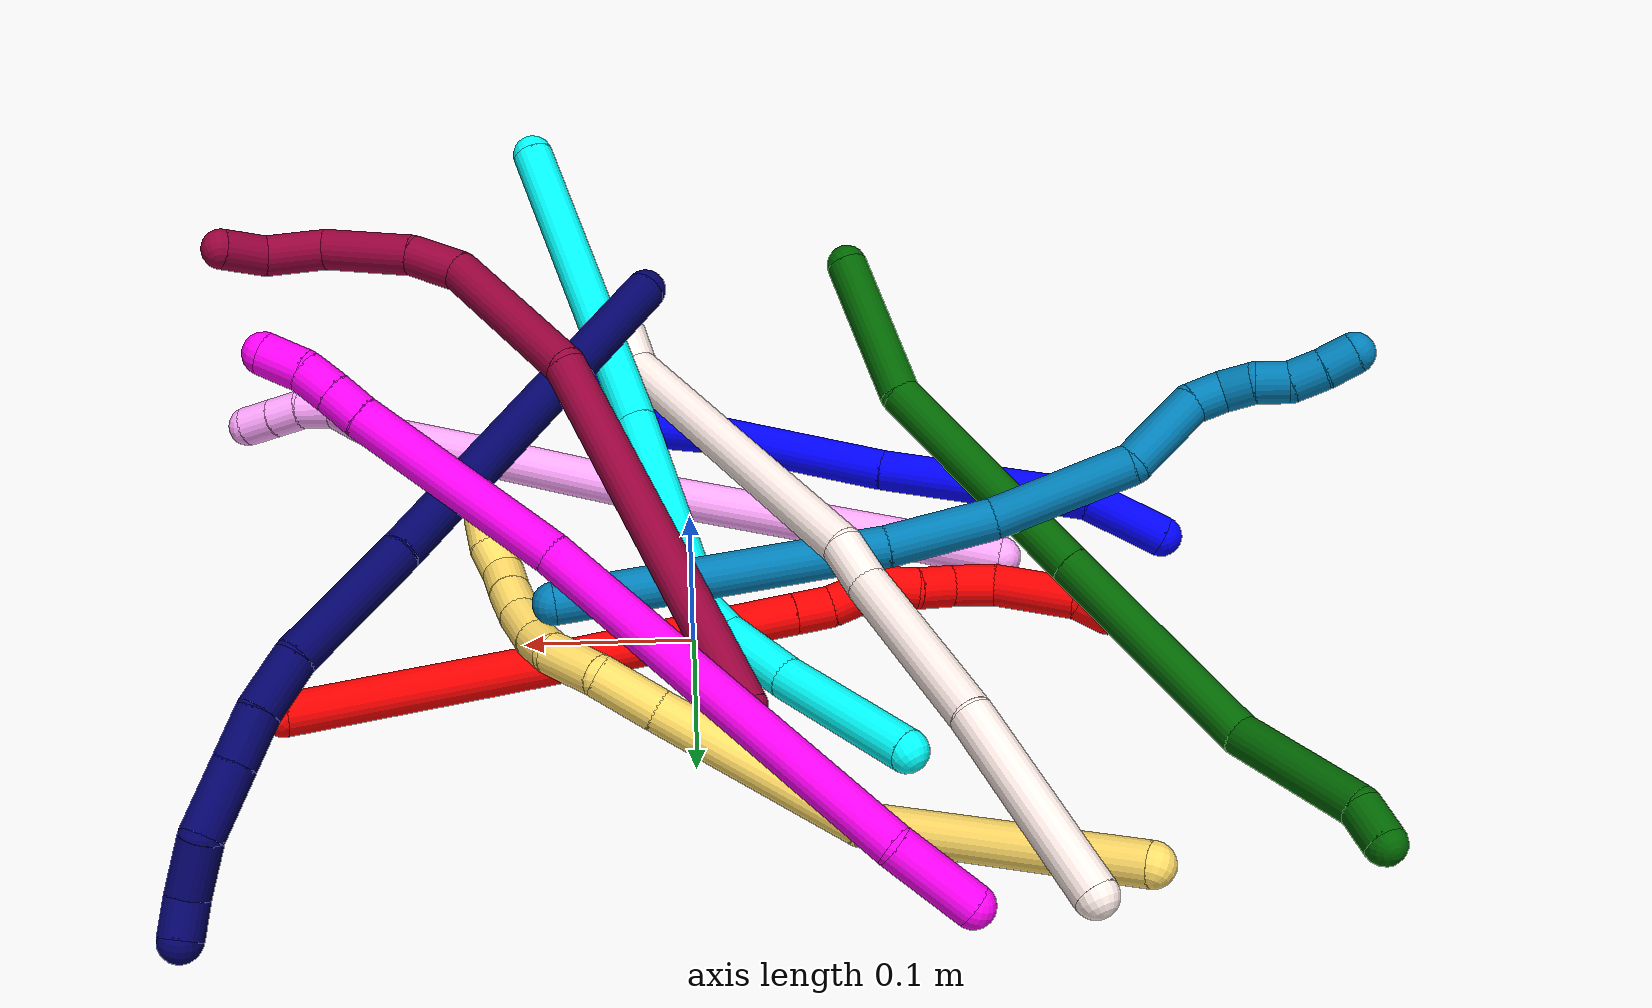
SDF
<sdf version="1.7">
 <world name="default">
  <plugin name="TubeGeneratorPlugin" filename="libtube_generator_plugin.so"/>
  <model name="photoneo_s_sensor">
   <static>1</static>
   <pose>0 0 2 1.57079 1.57079 3.14159</pose>
   <link name="link">
    <inertial><mass>0.1</mass></inertial>
    <sensor name="sensor" type="depth">
     <update_rate>30</update_rate>
     <camera>
      <horizontal_fov>1.22</horizontal_fov>
      <image><width>1920</width><height>1200</height><format>B8G8R8</format></image>
      <clip><near>0.1</near><far>4</far></clip>
      <depth_camera><output>points</output></depth_camera>
     </camera>
     <plugin name="camera_plugin" filename="libgazebo_ros_depth_camera.so">
      <baseline>0.2</baseline>
      <alwaysOn>1</alwaysOn>
      <updateRate>0.0</updateRate>
      <cameraName>camera_ir</cameraName>
      <imageTopicName>/camera/color/image_raw</imageTopicName>
      <cameraInfoTopicName>/camera/color/camera_info</cameraInfoTopicName>
      <depthImageTopicName>/camera/depth/image_raw</depthImageTopicName>
      <depthImageCameraInfoTopicName>/camera/depth/camera_info</depthImageCameraInfoTopicName>
      <pointCloudTopicName>/camera/depth/points</pointCloudTopicName>
      <frameName>fr_optical</frameName>
      <pointCloudCutoff>0.1</pointCloudCutoff>
      <pointCloudCutoffMax>2.0</pointCloudCutoffMax>
      <distortionK1>0</distortionK1>
      <distortionK2>0</distortionK2>
      <distortionK3>0</distortionK3>
      <distortionT1>0</distortionT1>
      <distortionT2>0</distortionT2>
      <CxPrime>0</CxPrime>
      <Cx>0</Cx>
      <Cy>0</Cy>
      <focalLength>0</focalLength>
      <hackBaseline>0</hackBaseline>
     </plugin>
    </sensor>
   </link>
  </model>
  <gravity>0 0 -9.8</gravity>
  <magnetic_field>6e-06 2.3e-05 -4.2e-05</magnetic_field>
  <atmosphere type="adiabatic"/>
  <physics name="default_physics" default="0" type="ode">
   <max_step_size>0.003</max_step_size>
   <real_time_factor>1</real_time_factor>
   <real_time_update_rate>1000</real_time_update_rate>
   <max_contacts>10000</max_contacts>
   <ode>
    <solver>
     <type>quick</type>
     <iters>100</iters>
     <sor>1.3</sor>
     <use_dynamic_moi_rescaling>0</use_dynamic_moi_rescaling>
    </solver>
    <constraints>
     <contact_max_correcting_vel>0</contact_max_correcting_vel>
     <contact_surface_layer>0.001</contact_surface_layer>
     <cfm>0</cfm>
     <erp>0.2</erp>
    </constraints>
   </ode>
  </physics>
  <scene><ambient>0.4 0.4 0.4 1</ambient><background>0.7 0.7 0.7 1</background><shadows>0</shadows></scene>
  <audio><device>default</device></audio>
  <spherical_coordinates>
   <surface_model>EARTH_WGS84</surface_model>
   <latitude_deg>0</latitude_deg>
   <longitude_deg>0</longitude_deg>
   <elevation>0</elevation>
   <heading_deg>0</heading_deg>
  </spherical_coordinates>
  <model name="bin">
   <static>1</static>
   <link name="bottom">
    <collision name="collision-bottom">
     <pose>0 0 -0.01 0 -0 0</pose>
     <geometry><box><size>0.8 0.6 0.02</size></box></geometry>
     <surface>
      <friction><ode><mu>100</mu><mu2>100</mu2></ode></friction>
      <contact><collide_bitmask>65535</collide_bitmask></contact>
     </surface>
    </collision>
   </link>
   <link name="west_wall">
    <collision name="collision-west_wall">
     <pose>-0.41 0 0.1 0 -0 0</pose>
     <geometry><box><size>0.02 0.6 0.2</size></box></geometry>
     <surface>
      <friction><ode><mu>100</mu><mu2>100</mu2></ode></friction>
      <contact><collide_bitmask>65535</collide_bitmask></contact>
     </surface>
    </collision>
   </link>
   <link name="east_wall">
    <collision name="collision-east_wall">
     <pose>0.41 0 0.1 0 -0 0</pose>
     <geometry><box><size>0.02 0.6 0.2</size></box></geometry>
     <surface>
      <friction><ode><mu>100</mu><mu2>100</mu2></ode></friction>
      <contact><collide_bitmask>65535</collide_bitmask></contact>
     </surface>
    </collision>
   </link>
   <link name="south_wall">
    <collision name="collision-south_wall">
     <pose>0 -0.31 0.1 0 -0 0</pose>
     <geometry><box><size>0.8 0.02 0.2</size></box></geometry>
     <surface>
      <friction><ode><mu>100</mu><mu2>100</mu2></ode></friction>
      <contact><collide_bitmask>65535</collide_bitmask></contact>
     </surface>
    </collision>
   </link>
   <link name="north_wall">
    <collision name="collision-north_wall">
     <pose>0 0.31 0.1 0 -0 0</pose>
     <geometry><box><size>0.8 0.02 0.2</size></box></geometry>
     <surface>
      <friction><ode><mu>100</mu><mu2>100</mu2></ode></friction>
      <contact><collide_bitmask>65535</collide_bitmask></contact>
     </surface>
    </collision>
   </link>
  </model>
  <model name="1">
   <static>0</static>
   <link name="1">
    <collision name="collision-cylinder-e_1_1_4">
     <pose>-0.032792 0.018142 -0.029388 -2.58853 -0.759489 1.90535</pose>
     <geometry><cylinder><radius>0.0125</radius><length>0.09525</length></cylinder></geometry>
     <surface>
      <friction><ode><mu>1.16</mu><mu2>1.16</mu2><slip1>0</slip1><slip2>0</slip2></ode></friction>
      <contact><ode><kp>1e+06</kp><kd>1</kd><max_vel>0</max_vel><min_depth>0.001</min_depth></ode></contact>
     </surface>
    </collision>
    <visual name="visual-cylinder-e_1_1_4">
     <pose>-0.032792 0.018142 -0.029388 -2.58853 -0.759489 1.90535</pose>
     <geometry><cylinder><radius>0.0125</radius><length>0.09525</length></cylinder></geometry>
     <material><ambient>0 0 1 1</ambient></material>
    </visual>
    <collision name="collision-cylinder-e_2_4_5">
     <pose>-0.084616 0.055157 -0.084108 -2.50127 -0.542245 1.39537</pose>
     <geometry><cylinder><radius>0.0125</radius><length>0.073759</length></cylinder></geometry>
     <surface>
      <friction><ode><mu>1.16</mu><mu2>1.16</mu2><slip1>0</slip1><slip2>0</slip2></ode></friction>
      <contact><ode><kp>1e+06</kp><kd>1</kd><max_vel>0</max_vel><min_depth>0.001</min_depth></ode></contact>
     </surface>
    </collision>
    <visual name="visual-cylinder-e_2_4_5">
     <pose>-0.084616 0.055157 -0.084108 -2.50127 -0.542245 1.39537</pose>
     <geometry><cylinder><radius>0.0125</radius><length>0.073759</length></cylinder></geometry>
     <material><ambient>0 0 1 1</ambient></material>
    </visual>
    <collision name="collision-cylinder-e_3_5_6">
     <pose>-0.108938 0.075839 -0.124562 -3.02256 -0.334287 2.46257</pose>
     <geometry><cylinder><radius>0.0125</radius><length>0.032246</length></cylinder></geometry>
     <surface>
      <friction><ode><mu>1.16</mu><mu2>1.16</mu2><slip1>0</slip1><slip2>0</slip2></ode></friction>
      <contact><ode><kp>1e+06</kp><kd>1</kd><max_vel>0</max_vel><min_depth>0.001</min_depth></ode></contact>
     </surface>
    </collision>
    <visual name="visual-cylinder-e_3_5_6">
     <pose>-0.108938 0.075839 -0.124562 -3.02256 -0.334287 2.46257</pose>
     <geometry><cylinder><radius>0.0125</radius><length>0.032246</length></cylinder></geometry>
     <material><ambient>0 0 1 1</ambient></material>
    </visual>
    <collision name="collision-cylinder-e_4_6_7">
     <pose>-0.132362 0.094624 -0.193464 -2.83583 -0.311115 1.58843</pose>
     <geometry><cylinder><radius>0.0125</radius><length>0.118479</length></cylinder></geometry>
     <surface>
      <friction><ode><mu>1.16</mu><mu2>1.16</mu2><slip1>0</slip1><slip2>0</slip2></ode></friction>
      <contact><ode><kp>1e+06</kp><kd>1</kd><max_vel>0</max_vel><min_depth>0.001</min_depth></ode></contact>
     </surface>
    </collision>
    <visual name="visual-cylinder-e_4_6_7">
     <pose>-0.132362 0.094624 -0.193464 -2.83583 -0.311115 1.58843</pose>
     <geometry><cylinder><radius>0.0125</radius><length>0.118479</length></cylinder></geometry>
     <material><ambient>0 0 1 1</ambient></material>
    </visual>
    <collision name="collision-cylinder-e_5_7_8">
     <pose>-0.167376 0.12816 -0.30773 -2.87436 -0.262935 1.55441</pose>
     <geometry><cylinder><radius>0.0125</radius><length>0.129888</length></cylinder></geometry>
     <surface>
      <friction><ode><mu>1.16</mu><mu2>1.16</mu2><slip1>0</slip1><slip2>0</slip2></ode></friction>
      <contact><ode><kp>1e+06</kp><kd>1</kd><max_vel>0</max_vel><min_depth>0.001</min_depth></ode></contact>
     </surface>
    </collision>
    <visual name="visual-cylinder-e_5_7_8">
     <pose>-0.167376 0.12816 -0.30773 -2.87436 -0.262935 1.55441</pose>
     <geometry><cylinder><radius>0.0125</radius><length>0.129888</length></cylinder></geometry>
     <material><ambient>0 0 1 1</ambient></material>
    </visual>
    <collision name="collision-cylinder-e_6_8_2">
     <pose>-0.191438 0.160143 -0.386791 -2.44861 -0.289119 0.766507</pose>
     <geometry><cylinder><radius>0.0125</radius><length>0.050379</length></cylinder></geometry>
     <surface>
      <friction><ode><mu>1.16</mu><mu2>1.16</mu2><slip1>0</slip1><slip2>0</slip2></ode></friction>
      <contact><ode><kp>1e+06</kp><kd>1</kd><max_vel>0</max_vel><min_depth>0.001</min_depth></ode></contact>
     </surface>
    </collision>
    <visual name="visual-cylinder-e_6_8_2">
     <pose>-0.191438 0.160143 -0.386791 -2.44861 -0.289119 0.766507</pose>
     <geometry><cylinder><radius>0.0125</radius><length>0.050379</length></cylinder></geometry>
     <material><ambient>0 0 1 1</ambient></material>
    </visual>
    <collision name="collision-sphere-2">
     <pose>-0.19862 0.175568 -0.405366 0 -0 0</pose>
     <geometry><sphere><radius>0.0125</radius></sphere></geometry>
     <surface>
      <friction><ode><mu>1.16</mu><mu2>1.16</mu2><slip1>0</slip1><slip2>0</slip2></ode></friction>
      <contact><ode><kp>1e+06</kp><kd>1</kd><max_vel>0</max_vel><min_depth>0.001</min_depth></ode></contact>
     </surface>
    </collision>
    <visual name="visual-sphere-2">
     <pose>-0.19862 0.175568 -0.405366 0 -0 0</pose>
     <geometry><sphere><radius>0.0125</radius></sphere></geometry>
     <material><ambient>0 0 1 1</ambient></material>
    </visual>
    <collision name="collision-sphere-4">
     <pose>-0.065584 0.036284 -0.058776 0 -0 0</pose>
     <geometry><sphere><radius>0.0125</radius></sphere></geometry>
     <surface>
      <friction><ode><mu>1.16</mu><mu2>1.16</mu2><slip1>0</slip1><slip2>0</slip2></ode></friction>
      <contact><ode><kp>1e+06</kp><kd>1</kd><max_vel>0</max_vel><min_depth>0.001</min_depth></ode></contact>
     </surface>
    </collision>
    <visual name="visual-sphere-4">
     <pose>-0.065584 0.036284 -0.058776 0 -0 0</pose>
     <geometry><sphere><radius>0.0125</radius></sphere></geometry>
     <material><ambient>0 0 1 1</ambient></material>
    </visual>
    <collision name="collision-sphere-1">
     <geometry><sphere><radius>0.0125</radius></sphere></geometry>
     <surface>
      <friction><ode><mu>1.16</mu><mu2>1.16</mu2><slip1>0</slip1><slip2>0</slip2></ode></friction>
      <contact><ode><kp>1e+06</kp><kd>1</kd><max_vel>0</max_vel><min_depth>0.001</min_depth></ode></contact>
     </surface>
    </collision>
    <visual name="visual-sphere-1">
     <geometry><sphere><radius>0.0125</radius></sphere></geometry>
     <material><ambient>0 0 1 1</ambient></material>
    </visual>
    <collision name="collision-sphere-8">
     <pose>-0.184257 0.144719 -0.368216 0 -0 0</pose>
     <geometry><sphere><radius>0.0125</radius></sphere></geometry>
     <surface>
      <friction><ode><mu>1.16</mu><mu2>1.16</mu2><slip1>0</slip1><slip2>0</slip2></ode></friction>
      <contact><ode><kp>1e+06</kp><kd>1</kd><max_vel>0</max_vel><min_depth>0.001</min_depth></ode></contact>
     </surface>
    </collision>
    <visual name="visual-sphere-8">
     <pose>-0.184257 0.144719 -0.368216 0 -0 0</pose>
     <geometry><sphere><radius>0.0125</radius></sphere></geometry>
     <material><ambient>0 0 1 1</ambient></material>
    </visual>
    <collision name="collision-sphere-5">
     <pose>-0.103648 0.07403 -0.109439 0 -0 0</pose>
     <geometry><sphere><radius>0.0125</radius></sphere></geometry>
     <surface>
      <friction><ode><mu>1.16</mu><mu2>1.16</mu2><slip1>0</slip1><slip2>0</slip2></ode></friction>
      <contact><ode><kp>1e+06</kp><kd>1</kd><max_vel>0</max_vel><min_depth>0.001</min_depth></ode></contact>
     </surface>
    </collision>
    <visual name="visual-sphere-5">
     <pose>-0.103648 0.07403 -0.109439 0 -0 0</pose>
     <geometry><sphere><radius>0.0125</radius></sphere></geometry>
     <material><ambient>0 0 1 1</ambient></material>
    </visual>
    <collision name="collision-sphere-6">
     <pose>-0.114228 0.077647 -0.139684 0 -0 0</pose>
     <geometry><sphere><radius>0.0125</radius></sphere></geometry>
     <surface>
      <friction><ode><mu>1.16</mu><mu2>1.16</mu2><slip1>0</slip1><slip2>0</slip2></ode></friction>
      <contact><ode><kp>1e+06</kp><kd>1</kd><max_vel>0</max_vel><min_depth>0.001</min_depth></ode></contact>
     </surface>
    </collision>
    <visual name="visual-sphere-6">
     <pose>-0.114228 0.077647 -0.139684 0 -0 0</pose>
     <geometry><sphere><radius>0.0125</radius></sphere></geometry>
     <material><ambient>0 0 1 1</ambient></material>
    </visual>
    <collision name="collision-sphere-7">
     <pose>-0.150496 0.1116 -0.247244 0 -0 0</pose>
     <geometry><sphere><radius>0.0125</radius></sphere></geometry>
     <surface>
      <friction><ode><mu>1.16</mu><mu2>1.16</mu2><slip1>0</slip1><slip2>0</slip2></ode></friction>
      <contact><ode><kp>1e+06</kp><kd>1</kd><max_vel>0</max_vel><min_depth>0.001</min_depth></ode></contact>
     </surface>
    </collision>
    <visual name="visual-sphere-7">
     <pose>-0.150496 0.1116 -0.247244 0 -0 0</pose>
     <geometry><sphere><radius>0.0125</radius></sphere></geometry>
     <material><ambient>0 0 1 1</ambient></material>
    </visual>
    <inertial>
     <pose>-0.119888 0.088334 -0.190795 0 -0 0</pose>
     <mass>0.5</mass>
     <inertia><ixx>0.000389</ixx><ixy>0</ixy><ixz>0</ixz><iyy>0.000501</iyy><iyz>0</iyz><izz>-8e-06</izz></inertia>
    </inertial>
   </link>
   <pose>0.140263 -0.288449 0.04923 -1.91668 -0.050495 -1.62883</pose>
  </model>
  <model name="2">
   <static>0</static>
   <link name="2">
    <collision name="collision-cylinder-e_1_1_4">
     <pose>-0.050805 -0.042242 0.048095 0.720696 -0.670873 -0.261217</pose>
     <geometry><cylinder><radius>0.0125</radius><length>0.163446</length></cylinder></geometry>
     <surface>
      <friction><ode><mu>1.16</mu><mu2>1.16</mu2><slip1>0</slip1><slip2>0</slip2></ode></friction>
      <contact><ode><kp>1e+06</kp><kd>1</kd><max_vel>0</max_vel><min_depth>0.001</min_depth></ode></contact>
     </surface>
    </collision>
    <visual name="visual-cylinder-e_1_1_4">
     <pose>-0.050805 -0.042242 0.048095 0.720696 -0.670873 -0.261217</pose>
     <geometry><cylinder><radius>0.0125</radius><length>0.163446</length></cylinder></geometry>
     <material><ambient>1 0 0 1</ambient></material>
    </visual>
    <collision name="collision-cylinder-e_2_4_5">
     <pose>-0.142047 -0.113597 0.144374 0.543505 -0.622906 -0.17893</pose>
     <geometry><cylinder><radius>0.0125</radius><length>0.138627</length></cylinder></geometry>
     <surface>
      <friction><ode><mu>1.16</mu><mu2>1.16</mu2><slip1>0</slip1><slip2>0</slip2></ode></friction>
      <contact><ode><kp>1e+06</kp><kd>1</kd><max_vel>0</max_vel><min_depth>0.001</min_depth></ode></contact>
     </surface>
    </collision>
    <visual name="visual-cylinder-e_2_4_5">
     <pose>-0.142047 -0.113597 0.144374 0.543505 -0.622906 -0.17893</pose>
     <geometry><cylinder><radius>0.0125</radius><length>0.138627</length></cylinder></geometry>
     <material><ambient>1 0 0 1</ambient></material>
    </visual>
    <collision name="collision-cylinder-e_3_5_6">
     <pose>-0.189291 -0.147559 0.200567 0.54446 -0.628536 -0.180981</pose>
     <geometry><cylinder><radius>0.0125</radius><length>0.023152</length></cylinder></geometry>
     <surface>
      <friction><ode><mu>1.16</mu><mu2>1.16</mu2><slip1>0</slip1><slip2>0</slip2></ode></friction>
      <contact><ode><kp>1e+06</kp><kd>1</kd><max_vel>0</max_vel><min_depth>0.001</min_depth></ode></contact>
     </surface>
    </collision>
    <visual name="visual-cylinder-e_3_5_6">
     <pose>-0.189291 -0.147559 0.200567 0.54446 -0.628536 -0.180981</pose>
     <geometry><cylinder><radius>0.0125</radius><length>0.023152</length></cylinder></geometry>
     <material><ambient>1 0 0 1</ambient></material>
    </visual>
    <collision name="collision-cylinder-e_4_6_7">
     <pose>-0.201625 -0.15825 0.221358 0.428647 -0.37481 -0.082505</pose>
     <geometry><cylinder><radius>0.0125</radius><length>0.030201</length></cylinder></geometry>
     <surface>
      <friction><ode><mu>1.16</mu><mu2>1.16</mu2><slip1>0</slip1><slip2>0</slip2></ode></friction>
      <contact><ode><kp>1e+06</kp><kd>1</kd><max_vel>0</max_vel><min_depth>0.001</min_depth></ode></contact>
     </surface>
    </collision>
    <visual name="visual-cylinder-e_4_6_7">
     <pose>-0.201625 -0.15825 0.221358 0.428647 -0.37481 -0.082505</pose>
     <geometry><cylinder><radius>0.0125</radius><length>0.030201</length></cylinder></geometry>
     <material><ambient>1 0 0 1</ambient></material>
    </visual>
    <collision name="collision-cylinder-e_5_7_8">
     <pose>-0.215981 -0.166853 0.241698 0.350323 -0.831529 -0.155953</pose>
     <geometry><cylinder><radius>0.0125</radius><length>0.023892</length></cylinder></geometry>
     <surface>
      <friction><ode><mu>1.16</mu><mu2>1.16</mu2><slip1>0</slip1><slip2>0</slip2></ode></friction>
      <contact><ode><kp>1e+06</kp><kd>1</kd><max_vel>0</max_vel><min_depth>0.001</min_depth></ode></contact>
     </surface>
    </collision>
    <visual name="visual-cylinder-e_5_7_8">
     <pose>-0.215981 -0.166853 0.241698 0.350323 -0.831529 -0.155953</pose>
     <geometry><cylinder><radius>0.0125</radius><length>0.023892</length></cylinder></geometry>
     <material><ambient>1 0 0 1</ambient></material>
    </visual>
    <collision name="collision-cylinder-e_6_8_9">
     <pose>-0.232592 -0.174588 0.255574 0.666995 -0.769238 -0.278644</pose>
     <geometry><cylinder><radius>0.0125</radius><length>0.022379</length></cylinder></geometry>
     <surface>
      <friction><ode><mu>1.16</mu><mu2>1.16</mu2><slip1>0</slip1><slip2>0</slip2></ode></friction>
      <contact><ode><kp>1e+06</kp><kd>1</kd><max_vel>0</max_vel><min_depth>0.001</min_depth></ode></contact>
     </surface>
    </collision>
    <visual name="visual-cylinder-e_6_8_9">
     <pose>-0.232592 -0.174588 0.255574 0.666995 -0.769238 -0.278644</pose>
     <geometry><cylinder><radius>0.0125</radius><length>0.022379</length></cylinder></geometry>
     <material><ambient>1 0 0 1</ambient></material>
    </visual>
    <collision name="collision-cylinder-e_7_9_10">
     <pose>-0.249132 -0.182058 0.271401 0.256696 -0.727594 -0.098197</pose>
     <geometry><cylinder><radius>0.0125</radius><length>0.026333</length></cylinder></geometry>
     <surface>
      <friction><ode><mu>1.16</mu><mu2>1.16</mu2><slip1>0</slip1><slip2>0</slip2></ode></friction>
      <contact><ode><kp>1e+06</kp><kd>1</kd><max_vel>0</max_vel><min_depth>0.001</min_depth></ode></contact>
     </surface>
    </collision>
    <visual name="visual-cylinder-e_7_9_10">
     <pose>-0.249132 -0.182058 0.271401 0.256696 -0.727594 -0.098197</pose>
     <geometry><cylinder><radius>0.0125</radius><length>0.026333</length></cylinder></geometry>
     <material><ambient>1 0 0 1</ambient></material>
    </visual>
    <collision name="collision-cylinder-e_8_10_11">
     <pose>-0.273363 -0.178949 0.300107 -0.284104 -0.658564 0.097665</pose>
     <geometry><cylinder><radius>0.0125</radius><length>0.05057</length></cylinder></geometry>
     <surface>
      <friction><ode><mu>1.16</mu><mu2>1.16</mu2><slip1>0</slip1><slip2>0</slip2></ode></friction>
      <contact><ode><kp>1e+06</kp><kd>1</kd><max_vel>0</max_vel><min_depth>0.001</min_depth></ode></contact>
     </surface>
    </collision>
    <visual name="visual-cylinder-e_8_10_11">
     <pose>-0.273363 -0.178949 0.300107 -0.284104 -0.658564 0.097665</pose>
     <geometry><cylinder><radius>0.0125</radius><length>0.05057</length></cylinder></geometry>
     <material><ambient>1 0 0 1</ambient></material>
    </visual>
    <collision name="collision-cylinder-e_9_11_2">
     <pose>-0.298665 -0.173022 0.323519 -0.076141 -1.16442 0.050139</pose>
     <geometry><cylinder><radius>0.0125</radius><length>0.021399</length></cylinder></geometry>
     <surface>
      <friction><ode><mu>1.16</mu><mu2>1.16</mu2><slip1>0</slip1><slip2>0</slip2></ode></friction>
      <contact><ode><kp>1e+06</kp><kd>1</kd><max_vel>0</max_vel><min_depth>0.001</min_depth></ode></contact>
     </surface>
    </collision>
    <visual name="visual-cylinder-e_9_11_2">
     <pose>-0.298665 -0.173022 0.323519 -0.076141 -1.16442 0.050139</pose>
     <geometry><cylinder><radius>0.0125</radius><length>0.021399</length></cylinder></geometry>
     <material><ambient>1 0 0 1</ambient></material>
    </visual>
    <collision name="collision-sphere-2">
     <pose>-0.308493 -0.1727 0.327737 0 -0 0</pose>
     <geometry><sphere><radius>0.0125</radius></sphere></geometry>
     <surface>
      <friction><ode><mu>1.16</mu><mu2>1.16</mu2><slip1>0</slip1><slip2>0</slip2></ode></friction>
      <contact><ode><kp>1e+06</kp><kd>1</kd><max_vel>0</max_vel><min_depth>0.001</min_depth></ode></contact>
     </surface>
    </collision>
    <visual name="visual-sphere-2">
     <pose>-0.308493 -0.1727 0.327737 0 -0 0</pose>
     <geometry><sphere><radius>0.0125</radius></sphere></geometry>
     <material><ambient>1 0 0 1</ambient></material>
    </visual>
    <collision name="collision-sphere-11">
     <pose>-0.288837 -0.173344 0.319302 0 -0 0</pose>
     <geometry><sphere><radius>0.0125</radius></sphere></geometry>
     <surface>
      <friction><ode><mu>1.16</mu><mu2>1.16</mu2><slip1>0</slip1><slip2>0</slip2></ode></friction>
      <contact><ode><kp>1e+06</kp><kd>1</kd><max_vel>0</max_vel><min_depth>0.001</min_depth></ode></contact>
     </surface>
    </collision>
    <visual name="visual-sphere-11">
     <pose>-0.288837 -0.173344 0.319302 0 -0 0</pose>
     <geometry><sphere><radius>0.0125</radius></sphere></geometry>
     <material><ambient>1 0 0 1</ambient></material>
    </visual>
    <collision name="collision-sphere-10">
     <pose>-0.257889 -0.184554 0.280911 0 -0 0</pose>
     <geometry><sphere><radius>0.0125</radius></sphere></geometry>
     <surface>
      <friction><ode><mu>1.16</mu><mu2>1.16</mu2><slip1>0</slip1><slip2>0</slip2></ode></friction>
      <contact><ode><kp>1e+06</kp><kd>1</kd><max_vel>0</max_vel><min_depth>0.001</min_depth></ode></contact>
     </surface>
    </collision>
    <visual name="visual-sphere-10">
     <pose>-0.257889 -0.184554 0.280911 0 -0 0</pose>
     <geometry><sphere><radius>0.0125</radius></sphere></geometry>
     <material><ambient>1 0 0 1</ambient></material>
    </visual>
    <collision name="collision-sphere-9">
     <pose>-0.240375 -0.179561 0.26189 0 -0 0</pose>
     <geometry><sphere><radius>0.0125</radius></sphere></geometry>
     <surface>
      <friction><ode><mu>1.16</mu><mu2>1.16</mu2><slip1>0</slip1><slip2>0</slip2></ode></friction>
      <contact><ode><kp>1e+06</kp><kd>1</kd><max_vel>0</max_vel><min_depth>0.001</min_depth></ode></contact>
     </surface>
    </collision>
    <visual name="visual-sphere-9">
     <pose>-0.240375 -0.179561 0.26189 0 -0 0</pose>
     <geometry><sphere><radius>0.0125</radius></sphere></geometry>
     <material><ambient>1 0 0 1</ambient></material>
    </visual>
    <collision name="collision-sphere-4">
     <pose>-0.10161 -0.084484 0.096191 0 -0 0</pose>
     <geometry><sphere><radius>0.0125</radius></sphere></geometry>
     <surface>
      <friction><ode><mu>1.16</mu><mu2>1.16</mu2><slip1>0</slip1><slip2>0</slip2></ode></friction>
      <contact><ode><kp>1e+06</kp><kd>1</kd><max_vel>0</max_vel><min_depth>0.001</min_depth></ode></contact>
     </surface>
    </collision>
    <visual name="visual-sphere-4">
     <pose>-0.10161 -0.084484 0.096191 0 -0 0</pose>
     <geometry><sphere><radius>0.0125</radius></sphere></geometry>
     <material><ambient>1 0 0 1</ambient></material>
    </visual>
    <collision name="collision-sphere-1">
     <geometry><sphere><radius>0.0125</radius></sphere></geometry>
     <surface>
      <friction><ode><mu>1.16</mu><mu2>1.16</mu2><slip1>0</slip1><slip2>0</slip2></ode></friction>
      <contact><ode><kp>1e+06</kp><kd>1</kd><max_vel>0</max_vel><min_depth>0.001</min_depth></ode></contact>
     </surface>
    </collision>
    <visual name="visual-sphere-1">
     <geometry><sphere><radius>0.0125</radius></sphere></geometry>
     <material><ambient>1 0 0 1</ambient></material>
    </visual>
    <collision name="collision-sphere-8">
     <pose>-0.224809 -0.169615 0.249258 0 -0 0</pose>
     <geometry><sphere><radius>0.0125</radius></sphere></geometry>
     <surface>
      <friction><ode><mu>1.16</mu><mu2>1.16</mu2><slip1>0</slip1><slip2>0</slip2></ode></friction>
      <contact><ode><kp>1e+06</kp><kd>1</kd><max_vel>0</max_vel><min_depth>0.001</min_depth></ode></contact>
     </surface>
    </collision>
    <visual name="visual-sphere-8">
     <pose>-0.224809 -0.169615 0.249258 0 -0 0</pose>
     <geometry><sphere><radius>0.0125</radius></sphere></geometry>
     <material><ambient>1 0 0 1</ambient></material>
    </visual>
    <collision name="collision-sphere-5">
     <pose>-0.182484 -0.142709 0.192558 0 -0 0</pose>
     <geometry><sphere><radius>0.0125</radius></sphere></geometry>
     <surface>
      <friction><ode><mu>1.16</mu><mu2>1.16</mu2><slip1>0</slip1><slip2>0</slip2></ode></friction>
      <contact><ode><kp>1e+06</kp><kd>1</kd><max_vel>0</max_vel><min_depth>0.001</min_depth></ode></contact>
     </surface>
    </collision>
    <visual name="visual-sphere-5">
     <pose>-0.182484 -0.142709 0.192558 0 -0 0</pose>
     <geometry><sphere><radius>0.0125</radius></sphere></geometry>
     <material><ambient>1 0 0 1</ambient></material>
    </visual>
    <collision name="collision-sphere-6">
     <pose>-0.196097 -0.152409 0.208577 0 -0 0</pose>
     <geometry><sphere><radius>0.0125</radius></sphere></geometry>
     <surface>
      <friction><ode><mu>1.16</mu><mu2>1.16</mu2><slip1>0</slip1><slip2>0</slip2></ode></friction>
      <contact><ode><kp>1e+06</kp><kd>1</kd><max_vel>0</max_vel><min_depth>0.001</min_depth></ode></contact>
     </surface>
    </collision>
    <visual name="visual-sphere-6">
     <pose>-0.196097 -0.152409 0.208577 0 -0 0</pose>
     <geometry><sphere><radius>0.0125</radius></sphere></geometry>
     <material><ambient>1 0 0 1</ambient></material>
    </visual>
    <collision name="collision-sphere-7">
     <pose>-0.207153 -0.164091 0.234139 0 -0 0</pose>
     <geometry><sphere><radius>0.0125</radius></sphere></geometry>
     <surface>
      <friction><ode><mu>1.16</mu><mu2>1.16</mu2><slip1>0</slip1><slip2>0</slip2></ode></friction>
      <contact><ode><kp>1e+06</kp><kd>1</kd><max_vel>0</max_vel><min_depth>0.001</min_depth></ode></contact>
     </surface>
    </collision>
    <visual name="visual-sphere-7">
     <pose>-0.207153 -0.164091 0.234139 0 -0 0</pose>
     <geometry><sphere><radius>0.0125</radius></sphere></geometry>
     <material><ambient>1 0 0 1</ambient></material>
    </visual>
    <inertial>
     <pose>-0.151216 -0.112574 0.159889 0 -0 0</pose>
     <mass>0.5</mass>
     <inertia>
      <ixx>0.00035</ixx>
      <ixy>0</ixy>
      <ixz>0</ixz>
      <iyy>0.000415</iyy>
      <iyz>0</iyz>
      <izz>0.000693</izz>
     </inertia>
    </inertial>
   </link>
   <pose>0.228571 0.079014 0.031714 0.231037 -0.78471 -0.362884</pose>
  </model>
  <model name="3">
   <static>0</static>
   <link name="3">
    <collision name="collision-cylinder-e_1_1_4">
     <pose>0.015715 0.008049 -0.098988 -3.06046 0.156934 -2.18855</pose>
     <geometry><cylinder><radius>0.0125</radius><length>0.201101</length></cylinder></geometry>
     <surface>
      <friction><ode><mu>1.16</mu><mu2>1.16</mu2><slip1>0</slip1><slip2>0</slip2></ode></friction>
      <contact><ode><kp>1e+06</kp><kd>1</kd><max_vel>0</max_vel><min_depth>0.001</min_depth></ode></contact>
     </surface>
    </collision>
    <visual name="visual-cylinder-e_1_1_4">
     <pose>0.015715 0.008049 -0.098988 -3.06046 0.156934 -2.18855</pose>
     <geometry><cylinder><radius>0.0125</radius><length>0.201101</length></cylinder></geometry>
     <material><ambient>0.003922 1 0.996078 1</ambient></material>
    </visual>
    <collision name="collision-cylinder-e_2_4_5">
     <pose>0.044223 0.027887 -0.262782 -2.96164 0.191832 -1.63507</pose>
     <geometry><cylinder><radius>0.0125</radius><length>0.1342</length></cylinder></geometry>
     <surface>
      <friction><ode><mu>1.16</mu><mu2>1.16</mu2><slip1>0</slip1><slip2>0</slip2></ode></friction>
      <contact><ode><kp>1e+06</kp><kd>1</kd><max_vel>0</max_vel><min_depth>0.001</min_depth></ode></contact>
     </surface>
    </collision>
    <visual name="visual-cylinder-e_2_4_5">
     <pose>0.044223 0.027887 -0.262782 -2.96164 0.191832 -1.63507</pose>
     <geometry><cylinder><radius>0.0125</radius><length>0.1342</length></cylinder></geometry>
     <material><ambient>0.003922 1 0.996078 1</ambient></material>
    </visual>
    <collision name="collision-cylinder-e_3_5_6">
     <pose>0.054472 0.040438 -0.337872 -3.06761 -0.241909 2.55045</pose>
     <geometry><cylinder><radius>0.0125</radius><length>0.021244</length></cylinder></geometry>
     <surface>
      <friction><ode><mu>1.16</mu><mu2>1.16</mu2><slip1>0</slip1><slip2>0</slip2></ode></friction>
      <contact><ode><kp>1e+06</kp><kd>1</kd><max_vel>0</max_vel><min_depth>0.001</min_depth></ode></contact>
     </surface>
    </collision>
    <visual name="visual-cylinder-e_3_5_6">
     <pose>0.054472 0.040438 -0.337872 -3.06761 -0.241909 2.55045</pose>
     <geometry><cylinder><radius>0.0125</radius><length>0.021244</length></cylinder></geometry>
     <material><ambient>0.003922 1 0.996078 1</ambient></material>
    </visual>
    <collision name="collision-cylinder-e_4_6_7">
     <pose>0.044601 0.05094 -0.370272 -2.72676 -0.29438 1.22751</pose>
     <geometry><cylinder><radius>0.0125</radius><length>0.050501</length></cylinder></geometry>
     <surface>
      <friction><ode><mu>1.16</mu><mu2>1.16</mu2><slip1>0</slip1><slip2>0</slip2></ode></friction>
      <contact><ode><kp>1e+06</kp><kd>1</kd><max_vel>0</max_vel><min_depth>0.001</min_depth></ode></contact>
     </surface>
    </collision>
    <visual name="visual-cylinder-e_4_6_7">
     <pose>0.044601 0.05094 -0.370272 -2.72676 -0.29438 1.22751</pose>
     <geometry><cylinder><radius>0.0125</radius><length>0.050501</length></cylinder></geometry>
     <material><ambient>0.003922 1 0.996078 1</ambient></material>
    </visual>
    <collision name="collision-cylinder-e_5_7_2">
     <pose>0.022298 0.082587 -0.430542 -2.62038 -0.328094 1.11106</pose>
     <geometry><cylinder><radius>0.0125</radius><length>0.092953</length></cylinder></geometry>
     <surface>
      <friction><ode><mu>1.16</mu><mu2>1.16</mu2><slip1>0</slip1><slip2>0</slip2></ode></friction>
      <contact><ode><kp>1e+06</kp><kd>1</kd><max_vel>0</max_vel><min_depth>0.001</min_depth></ode></contact>
     </surface>
    </collision>
    <visual name="visual-cylinder-e_5_7_2">
     <pose>0.022298 0.082587 -0.430542 -2.62038 -0.328094 1.11106</pose>
     <geometry><cylinder><radius>0.0125</radius><length>0.092953</length></cylinder></geometry>
     <material><ambient>0.003922 1 0.996078 1</ambient></material>
    </visual>
    <collision name="collision-sphere-2">
     <pose>0.007321 0.104495 -0.468697 0 -0 0</pose>
     <geometry><sphere><radius>0.0125</radius></sphere></geometry>
     <surface>
      <friction><ode><mu>1.16</mu><mu2>1.16</mu2><slip1>0</slip1><slip2>0</slip2></ode></friction>
      <contact><ode><kp>1e+06</kp><kd>1</kd><max_vel>0</max_vel><min_depth>0.001</min_depth></ode></contact>
     </surface>
    </collision>
    <visual name="visual-sphere-2">
     <pose>0.007321 0.104495 -0.468697 0 -0 0</pose>
     <geometry><sphere><radius>0.0125</radius></sphere></geometry>
     <material><ambient>0.003922 1 0.996078 1</ambient></material>
    </visual>
    <collision name="collision-sphere-7">
     <pose>0.037275 0.060679 -0.392387 0 -0 0</pose>
     <geometry><sphere><radius>0.0125</radius></sphere></geometry>
     <surface>
      <friction><ode><mu>1.16</mu><mu2>1.16</mu2><slip1>0</slip1><slip2>0</slip2></ode></friction>
      <contact><ode><kp>1e+06</kp><kd>1</kd><max_vel>0</max_vel><min_depth>0.001</min_depth></ode></contact>
     </surface>
    </collision>
    <visual name="visual-sphere-7">
     <pose>0.037275 0.060679 -0.392387 0 -0 0</pose>
     <geometry><sphere><radius>0.0125</radius></sphere></geometry>
     <material><ambient>0.003922 1 0.996078 1</ambient></material>
    </visual>
    <collision name="collision-sphere-6">
     <pose>0.051927 0.041201 -0.348157 0 -0 0</pose>
     <geometry><sphere><radius>0.0125</radius></sphere></geometry>
     <surface>
      <friction><ode><mu>1.16</mu><mu2>1.16</mu2><slip1>0</slip1><slip2>0</slip2></ode></friction>
      <contact><ode><kp>1e+06</kp><kd>1</kd><max_vel>0</max_vel><min_depth>0.001</min_depth></ode></contact>
     </surface>
    </collision>
    <visual name="visual-sphere-6">
     <pose>0.051927 0.041201 -0.348157 0 -0 0</pose>
     <geometry><sphere><radius>0.0125</radius></sphere></geometry>
     <material><ambient>0.003922 1 0.996078 1</ambient></material>
    </visual>
    <collision name="collision-sphere-5">
     <pose>0.057016 0.039676 -0.327588 0 -0 0</pose>
     <geometry><sphere><radius>0.0125</radius></sphere></geometry>
     <surface>
      <friction><ode><mu>1.16</mu><mu2>1.16</mu2><slip1>0</slip1><slip2>0</slip2></ode></friction>
      <contact><ode><kp>1e+06</kp><kd>1</kd><max_vel>0</max_vel><min_depth>0.001</min_depth></ode></contact>
     </surface>
    </collision>
    <visual name="visual-sphere-5">
     <pose>0.057016 0.039676 -0.327588 0 -0 0</pose>
     <geometry><sphere><radius>0.0125</radius></sphere></geometry>
     <material><ambient>0.003922 1 0.996078 1</ambient></material>
    </visual>
    <collision name="collision-sphere-1">
     <geometry><sphere><radius>0.0125</radius></sphere></geometry>
     <surface>
      <friction><ode><mu>1.16</mu><mu2>1.16</mu2><slip1>0</slip1><slip2>0</slip2></ode></friction>
      <contact><ode><kp>1e+06</kp><kd>1</kd><max_vel>0</max_vel><min_depth>0.001</min_depth></ode></contact>
     </surface>
    </collision>
    <visual name="visual-sphere-1">
     <geometry><sphere><radius>0.0125</radius></sphere></geometry>
     <material><ambient>0.003922 1 0.996078 1</ambient></material>
    </visual>
    <collision name="collision-sphere-4">
     <pose>0.03143 0.016097 -0.197976 0 -0 0</pose>
     <geometry><sphere><radius>0.0125</radius></sphere></geometry>
     <surface>
      <friction><ode><mu>1.16</mu><mu2>1.16</mu2><slip1>0</slip1><slip2>0</slip2></ode></friction>
      <contact><ode><kp>1e+06</kp><kd>1</kd><max_vel>0</max_vel><min_depth>0.001</min_depth></ode></contact>
     </surface>
    </collision>
    <visual name="visual-sphere-4">
     <pose>0.03143 0.016097 -0.197976 0 -0 0</pose>
     <geometry><sphere><radius>0.0125</radius></sphere></geometry>
     <material><ambient>0.003922 1 0.996078 1</ambient></material>
    </visual>
    <inertial>
     <pose>0.029155 0.032939 -0.242139 0 -0 0</pose>
     <mass>0.5</mass>
     <inertia>
      <ixx>-0.001055</ixx>
      <ixy>0</ixy>
      <ixz>0</ixz>
      <iyy>-0.000269</iyy>
      <iyz>0</iyz>
      <izz>-0.000286</izz>
     </inertia>
    </inertial>
   </link>
   <pose>0.094748 -0.288039 0.151462 1.12606 0.223378 0.426385</pose>
  </model>
  <model name="4">
   <static>0</static>
   <link name="4">
    <collision name="collision-cylinder-e_1_1_4">
     <pose>0.093295 0.011278 0.053296 -0.208542 1.04229 -0.120012</pose>
     <geometry><cylinder><radius>0.0125</radius><length>0.21607</length></cylinder></geometry>
     <surface>
      <friction><ode><mu>1.16</mu><mu2>1.16</mu2><slip1>0</slip1><slip2>0</slip2></ode></friction>
      <contact><ode><kp>1e+06</kp><kd>1</kd><max_vel>0</max_vel><min_depth>0.001</min_depth></ode></contact>
     </surface>
    </collision>
    <visual name="visual-cylinder-e_1_1_4">
     <pose>0.093295 0.011278 0.053296 -0.208542 1.04229 -0.120012</pose>
     <geometry><cylinder><radius>0.0125</radius><length>0.21607</length></cylinder></geometry>
     <material><ambient>1 0.65098 0.996078 1</ambient></material>
    </visual>
    <collision name="collision-cylinder-e_2_4_5">
     <pose>0.232696 0.030049 0.133267 -0.273791 1.02968 -0.155552</pose>
     <geometry><cylinder><radius>0.0125</radius><length>0.107584</length></cylinder></geometry>
     <surface>
      <friction><ode><mu>1.16</mu><mu2>1.16</mu2><slip1>0</slip1><slip2>0</slip2></ode></friction>
      <contact><ode><kp>1e+06</kp><kd>1</kd><max_vel>0</max_vel><min_depth>0.001</min_depth></ode></contact>
     </surface>
    </collision>
    <visual name="visual-cylinder-e_2_4_5">
     <pose>0.232696 0.030049 0.133267 -0.273791 1.02968 -0.155552</pose>
     <geometry><cylinder><radius>0.0125</radius><length>0.107584</length></cylinder></geometry>
     <material><ambient>1 0.65098 0.996078 1</ambient></material>
    </visual>
    <collision name="collision-cylinder-e_3_5_6">
     <pose>0.306263 0.041008 0.17919 -0.178263 0.951941 -0.092073</pose>
     <geometry><cylinder><radius>0.0125</radius><length>0.067424</length></cylinder></geometry>
     <surface>
      <friction><ode><mu>1.16</mu><mu2>1.16</mu2><slip1>0</slip1><slip2>0</slip2></ode></friction>
      <contact><ode><kp>1e+06</kp><kd>1</kd><max_vel>0</max_vel><min_depth>0.001</min_depth></ode></contact>
     </surface>
    </collision>
    <visual name="visual-cylinder-e_3_5_6">
     <pose>0.306263 0.041008 0.17919 -0.178263 0.951941 -0.092073</pose>
     <geometry><cylinder><radius>0.0125</radius><length>0.067424</length></cylinder></geometry>
     <material><ambient>1 0.65098 0.996078 1</ambient></material>
    </visual>
    <collision name="collision-cylinder-e_4_6_7">
     <pose>0.342868 0.048306 0.202809 -0.71936 1.00461 -0.407386</pose>
     <geometry><cylinder><radius>0.0125</radius><length>0.021672</length></cylinder></geometry>
     <surface>
      <friction><ode><mu>1.16</mu><mu2>1.16</mu2><slip1>0</slip1><slip2>0</slip2></ode></friction>
      <contact><ode><kp>1e+06</kp><kd>1</kd><max_vel>0</max_vel><min_depth>0.001</min_depth></ode></contact>
     </surface>
    </collision>
    <visual name="visual-cylinder-e_4_6_7">
     <pose>0.342868 0.048306 0.202809 -0.71936 1.00461 -0.407386</pose>
     <geometry><cylinder><radius>0.0125</radius><length>0.021672</length></cylinder></geometry>
     <material><ambient>1 0.65098 0.996078 1</ambient></material>
    </visual>
    <collision name="collision-cylinder-e_5_7_8">
     <pose>0.359618 0.056099 0.213673 -0.548149 0.785317 -0.231841</pose>
     <geometry><cylinder><radius>0.0125</radius><length>0.021511</length></cylinder></geometry>
     <surface>
      <friction><ode><mu>1.16</mu><mu2>1.16</mu2><slip1>0</slip1><slip2>0</slip2></ode></friction>
      <contact><ode><kp>1e+06</kp><kd>1</kd><max_vel>0</max_vel><min_depth>0.001</min_depth></ode></contact>
     </surface>
    </collision>
    <visual name="visual-cylinder-e_5_7_8">
     <pose>0.359618 0.056099 0.213673 -0.548149 0.785317 -0.231841</pose>
     <geometry><cylinder><radius>0.0125</radius><length>0.021511</length></cylinder></geometry>
     <material><ambient>1 0.65098 0.996078 1</ambient></material>
    </visual>
    <collision name="collision-cylinder-e_6_8_9">
     <pose>0.376875 0.059056 0.226956 0.147217 0.952536 0.076047</pose>
     <geometry><cylinder><radius>0.0125</radius><length>0.02369</length></cylinder></geometry>
     <surface>
      <friction><ode><mu>1.16</mu><mu2>1.16</mu2><slip1>0</slip1><slip2>0</slip2></ode></friction>
      <contact><ode><kp>1e+06</kp><kd>1</kd><max_vel>0</max_vel><min_depth>0.001</min_depth></ode></contact>
     </surface>
    </collision>
    <visual name="visual-cylinder-e_6_8_9">
     <pose>0.376875 0.059056 0.226956 0.147217 0.952536 0.076047</pose>
     <geometry><cylinder><radius>0.0125</radius><length>0.02369</length></cylinder></geometry>
     <material><ambient>1 0.65098 0.996078 1</ambient></material>
    </visual>
    <collision name="collision-cylinder-e_7_9_10">
     <pose>0.394375 0.054414 0.239543 0.560124 0.853819 0.260192</pose>
     <geometry><cylinder><radius>0.0125</radius><length>0.020823</length></cylinder></geometry>
     <surface>
      <friction><ode><mu>1.16</mu><mu2>1.16</mu2><slip1>0</slip1><slip2>0</slip2></ode></friction>
      <contact><ode><kp>1e+06</kp><kd>1</kd><max_vel>0</max_vel><min_depth>0.001</min_depth></ode></contact>
     </surface>
    </collision>
    <visual name="visual-cylinder-e_7_9_10">
     <pose>0.394375 0.054414 0.239543 0.560124 0.853819 0.260192</pose>
     <geometry><cylinder><radius>0.0125</radius><length>0.020823</length></cylinder></geometry>
     <material><ambient>1 0.65098 0.996078 1</ambient></material>
    </visual>
    <collision name="collision-cylinder-e_8_10_2">
     <pose>0.410061 0.047081 0.251465 0.543004 0.830895 0.244373</pose>
     <geometry><cylinder><radius>0.0125</radius><length>0.021227</length></cylinder></geometry>
     <surface>
      <friction><ode><mu>1.16</mu><mu2>1.16</mu2><slip1>0</slip1><slip2>0</slip2></ode></friction>
      <contact><ode><kp>1e+06</kp><kd>1</kd><max_vel>0</max_vel><min_depth>0.001</min_depth></ode></contact>
     </surface>
    </collision>
    <visual name="visual-cylinder-e_8_10_2">
     <pose>0.410061 0.047081 0.251465 0.543004 0.830895 0.244373</pose>
     <geometry><cylinder><radius>0.0125</radius><length>0.021227</length></cylinder></geometry>
     <material><ambient>1 0.65098 0.996078 1</ambient></material>
    </visual>
    <collision name="collision-sphere-2">
     <pose>0.4179 0.043384 0.257592 0 -0 0</pose>
     <geometry><sphere><radius>0.0125</radius></sphere></geometry>
     <surface>
      <friction><ode><mu>1.16</mu><mu2>1.16</mu2><slip1>0</slip1><slip2>0</slip2></ode></friction>
      <contact><ode><kp>1e+06</kp><kd>1</kd><max_vel>0</max_vel><min_depth>0.001</min_depth></ode></contact>
     </surface>
    </collision>
    <visual name="visual-sphere-2">
     <pose>0.4179 0.043384 0.257592 0 -0 0</pose>
     <geometry><sphere><radius>0.0125</radius></sphere></geometry>
     <material><ambient>1 0.65098 0.996078 1</ambient></material>
    </visual>
    <collision name="collision-sphere-10">
     <pose>0.402223 0.050779 0.245339 0 -0 0</pose>
     <geometry><sphere><radius>0.0125</radius></sphere></geometry>
     <surface>
      <friction><ode><mu>1.16</mu><mu2>1.16</mu2><slip1>0</slip1><slip2>0</slip2></ode></friction>
      <contact><ode><kp>1e+06</kp><kd>1</kd><max_vel>0</max_vel><min_depth>0.001</min_depth></ode></contact>
     </surface>
    </collision>
    <visual name="visual-sphere-10">
     <pose>0.402223 0.050779 0.245339 0 -0 0</pose>
     <geometry><sphere><radius>0.0125</radius></sphere></geometry>
     <material><ambient>1 0.65098 0.996078 1</ambient></material>
    </visual>
    <collision name="collision-sphere-9">
     <pose>0.386527 0.058048 0.233747 0 -0 0</pose>
     <geometry><sphere><radius>0.0125</radius></sphere></geometry>
     <surface>
      <friction><ode><mu>1.16</mu><mu2>1.16</mu2><slip1>0</slip1><slip2>0</slip2></ode></friction>
      <contact><ode><kp>1e+06</kp><kd>1</kd><max_vel>0</max_vel><min_depth>0.001</min_depth></ode></contact>
     </surface>
    </collision>
    <visual name="visual-sphere-9">
     <pose>0.386527 0.058048 0.233747 0 -0 0</pose>
     <geometry><sphere><radius>0.0125</radius></sphere></geometry>
     <material><ambient>1 0.65098 0.996078 1</ambient></material>
    </visual>
    <collision name="collision-sphere-4">
     <pose>0.186589 0.022557 0.106591 0 -0 0</pose>
     <geometry><sphere><radius>0.0125</radius></sphere></geometry>
     <surface>
      <friction><ode><mu>1.16</mu><mu2>1.16</mu2><slip1>0</slip1><slip2>0</slip2></ode></friction>
      <contact><ode><kp>1e+06</kp><kd>1</kd><max_vel>0</max_vel><min_depth>0.001</min_depth></ode></contact>
     </surface>
    </collision>
    <visual name="visual-sphere-4">
     <pose>0.186589 0.022557 0.106591 0 -0 0</pose>
     <geometry><sphere><radius>0.0125</radius></sphere></geometry>
     <material><ambient>1 0.65098 0.996078 1</ambient></material>
    </visual>
    <collision name="collision-sphere-1">
     <geometry><sphere><radius>0.0125</radius></sphere></geometry>
     <surface>
      <friction><ode><mu>1.16</mu><mu2>1.16</mu2><slip1>0</slip1><slip2>0</slip2></ode></friction>
      <contact><ode><kp>1e+06</kp><kd>1</kd><max_vel>0</max_vel><min_depth>0.001</min_depth></ode></contact>
     </surface>
    </collision>
    <visual name="visual-sphere-1">
     <geometry><sphere><radius>0.0125</radius></sphere></geometry>
     <material><ambient>1 0.65098 0.996078 1</ambient></material>
    </visual>
    <collision name="collision-sphere-8">
     <pose>0.367222 0.060063 0.220164 0 -0 0</pose>
     <geometry><sphere><radius>0.0125</radius></sphere></geometry>
     <surface>
      <friction><ode><mu>1.16</mu><mu2>1.16</mu2><slip1>0</slip1><slip2>0</slip2></ode></friction>
      <contact><ode><kp>1e+06</kp><kd>1</kd><max_vel>0</max_vel><min_depth>0.001</min_depth></ode></contact>
     </surface>
    </collision>
    <visual name="visual-sphere-8">
     <pose>0.367222 0.060063 0.220164 0 -0 0</pose>
     <geometry><sphere><radius>0.0125</radius></sphere></geometry>
     <material><ambient>1 0.65098 0.996078 1</ambient></material>
    </visual>
    <collision name="collision-sphere-5">
     <pose>0.278803 0.03754 0.159943 0 -0 0</pose>
     <geometry><sphere><radius>0.0125</radius></sphere></geometry>
     <surface>
      <friction><ode><mu>1.16</mu><mu2>1.16</mu2><slip1>0</slip1><slip2>0</slip2></ode></friction>
      <contact><ode><kp>1e+06</kp><kd>1</kd><max_vel>0</max_vel><min_depth>0.001</min_depth></ode></contact>
     </surface>
    </collision>
    <visual name="visual-sphere-5">
     <pose>0.278803 0.03754 0.159943 0 -0 0</pose>
     <geometry><sphere><radius>0.0125</radius></sphere></geometry>
     <material><ambient>1 0.65098 0.996078 1</ambient></material>
    </visual>
    <collision name="collision-sphere-6">
     <pose>0.333723 0.044476 0.198437 0 -0 0</pose>
     <geometry><sphere><radius>0.0125</radius></sphere></geometry>
     <surface>
      <friction><ode><mu>1.16</mu><mu2>1.16</mu2><slip1>0</slip1><slip2>0</slip2></ode></friction>
      <contact><ode><kp>1e+06</kp><kd>1</kd><max_vel>0</max_vel><min_depth>0.001</min_depth></ode></contact>
     </surface>
    </collision>
    <visual name="visual-sphere-6">
     <pose>0.333723 0.044476 0.198437 0 -0 0</pose>
     <geometry><sphere><radius>0.0125</radius></sphere></geometry>
     <material><ambient>1 0.65098 0.996078 1</ambient></material>
    </visual>
    <collision name="collision-sphere-7">
     <pose>0.352013 0.052136 0.207181 0 -0 0</pose>
     <geometry><sphere><radius>0.0125</radius></sphere></geometry>
     <surface>
      <friction><ode><mu>1.16</mu><mu2>1.16</mu2><slip1>0</slip1><slip2>0</slip2></ode></friction>
      <contact><ode><kp>1e+06</kp><kd>1</kd><max_vel>0</max_vel><min_depth>0.001</min_depth></ode></contact>
     </surface>
    </collision>
    <visual name="visual-sphere-7">
     <pose>0.352013 0.052136 0.207181 0 -0 0</pose>
     <geometry><sphere><radius>0.0125</radius></sphere></geometry>
     <material><ambient>1 0.65098 0.996078 1</ambient></material>
    </visual>
    <inertial>
     <pose>0.213705 0.028439 0.125257 0 -0 0</pose>
     <mass>0.5</mass>
     <inertia>
      <ixx>0.000473</ixx>
      <ixy>0</ixy>
      <ixz>0</ixz>
      <iyy>0.000927</iyy>
      <iyz>0</iyz>
      <izz>-0.000942</izz>
     </inertia>
    </inertial>
   </link>
   <pose>-0.187066 -0.05018 0.013441 2.08995 -0.209273 0.227923</pose>
  </model>
  <model name="5">
   <static>0</static>
   <link name="5">
    <collision name="collision-cylinder-e_1_1_4">
     <pose>0.079918 -0.02081 0.002942 1.43035 1.31364 1.18017</pose>
     <geometry><cylinder><radius>0.0125</radius><length>0.165271</length></cylinder></geometry>
     <surface>
      <friction><ode><mu>1.16</mu><mu2>1.16</mu2><slip1>0</slip1><slip2>0</slip2></ode></friction>
      <contact><ode><kp>1e+06</kp><kd>1</kd><max_vel>0</max_vel><min_depth>0.001</min_depth></ode></contact>
     </surface>
    </collision>
    <visual name="visual-cylinder-e_1_1_4">
     <pose>0.079918 -0.02081 0.002942 1.43035 1.31364 1.18017</pose>
     <geometry><cylinder><radius>0.0125</radius><length>0.165271</length></cylinder></geometry>
     <material><ambient>1 0.858824 0.4 1</ambient></material>
    </visual>
    <collision name="collision-cylinder-e_2_4_5">
     <pose>0.208068 -0.081679 -0.008155 1.90789 0.849092 1.13496</pose>
     <geometry><cylinder><radius>0.0125</radius><length>0.1285</length></cylinder></geometry>
     <surface>
      <friction><ode><mu>1.16</mu><mu2>1.16</mu2><slip1>0</slip1><slip2>0</slip2></ode></friction>
      <contact><ode><kp>1e+06</kp><kd>1</kd><max_vel>0</max_vel><min_depth>0.001</min_depth></ode></contact>
     </surface>
    </collision>
    <visual name="visual-cylinder-e_2_4_5">
     <pose>0.208068 -0.081679 -0.008155 1.90789 0.849092 1.13496</pose>
     <geometry><cylinder><radius>0.0125</radius><length>0.1285</length></cylinder></geometry>
     <material><ambient>1 0.858824 0.4 1</ambient></material>
    </visual>
    <collision name="collision-cylinder-e_3_5_6">
     <pose>0.269693 -0.135125 -0.026304 1.86859 0.763117 0.994656</pose>
     <geometry><cylinder><radius>0.0125</radius><length>0.038755</length></cylinder></geometry>
     <surface>
      <friction><ode><mu>1.16</mu><mu2>1.16</mu2><slip1>0</slip1><slip2>0</slip2></ode></friction>
      <contact><ode><kp>1e+06</kp><kd>1</kd><max_vel>0</max_vel><min_depth>0.001</min_depth></ode></contact>
     </surface>
    </collision>
    <visual name="visual-cylinder-e_3_5_6">
     <pose>0.269693 -0.135125 -0.026304 1.86859 0.763117 0.994656</pose>
     <geometry><cylinder><radius>0.0125</radius><length>0.038755</length></cylinder></geometry>
     <material><ambient>1 0.858824 0.4 1</ambient></material>
    </visual>
    <collision name="collision-cylinder-e_4_6_7">
     <pose>0.29991 -0.152922 -0.03492 2.36718 1.21219 2.07799</pose>
     <geometry><cylinder><radius>0.0125</radius><length>0.035932</length></cylinder></geometry>
     <surface>
      <friction><ode><mu>1.16</mu><mu2>1.16</mu2><slip1>0</slip1><slip2>0</slip2></ode></friction>
      <contact><ode><kp>1e+06</kp><kd>1</kd><max_vel>0</max_vel><min_depth>0.001</min_depth></ode></contact>
     </surface>
    </collision>
    <visual name="visual-cylinder-e_4_6_7">
     <pose>0.29991 -0.152922 -0.03492 2.36718 1.21219 2.07799</pose>
     <geometry><cylinder><radius>0.0125</radius><length>0.035932</length></cylinder></geometry>
     <material><ambient>1 0.858824 0.4 1</ambient></material>
    </visual>
    <collision name="collision-cylinder-e_5_7_8">
     <pose>0.326396 -0.156684 -0.043989 -3.00053 1.12591 -2.91863</pose>
     <geometry><cylinder><radius>0.0125</radius><length>0.021409</length></cylinder></geometry>
     <surface>
      <friction><ode><mu>1.16</mu><mu2>1.16</mu2><slip1>0</slip1><slip2>0</slip2></ode></friction>
      <contact><ode><kp>1e+06</kp><kd>1</kd><max_vel>0</max_vel><min_depth>0.001</min_depth></ode></contact>
     </surface>
    </collision>
    <visual name="visual-cylinder-e_5_7_8">
     <pose>0.326396 -0.156684 -0.043989 -3.00053 1.12591 -2.91863</pose>
     <geometry><cylinder><radius>0.0125</radius><length>0.021409</length></cylinder></geometry>
     <material><ambient>1 0.858824 0.4 1</ambient></material>
    </visual>
    <collision name="collision-cylinder-e_6_8_9">
     <pose>0.347075 -0.155518 -0.056263 -3.07446 0.958904 -3.0126</pose>
     <geometry><cylinder><radius>0.0125</radius><length>0.026918</length></cylinder></geometry>
     <surface>
      <friction><ode><mu>1.16</mu><mu2>1.16</mu2><slip1>0</slip1><slip2>0</slip2></ode></friction>
      <contact><ode><kp>1e+06</kp><kd>1</kd><max_vel>0</max_vel><min_depth>0.001</min_depth></ode></contact>
     </surface>
    </collision>
    <visual name="visual-cylinder-e_6_8_9">
     <pose>0.347075 -0.155518 -0.056263 -3.07446 0.958904 -3.0126</pose>
     <geometry><cylinder><radius>0.0125</radius><length>0.026918</length></cylinder></geometry>
     <material><ambient>1 0.858824 0.4 1</ambient></material>
    </visual>
    <collision name="collision-cylinder-e_7_9_10">
     <pose>0.366569 -0.154912 -0.071569 -3.13013 0.840402 -3.11594</pose>
     <geometry><cylinder><radius>0.0125</radius><length>0.022761</length></cylinder></geometry>
     <surface>
      <friction><ode><mu>1.16</mu><mu2>1.16</mu2><slip1>0</slip1><slip2>0</slip2></ode></friction>
      <contact><ode><kp>1e+06</kp><kd>1</kd><max_vel>0</max_vel><min_depth>0.001</min_depth></ode></contact>
     </surface>
    </collision>
    <visual name="visual-cylinder-e_7_9_10">
     <pose>0.366569 -0.154912 -0.071569 -3.13013 0.840402 -3.11594</pose>
     <geometry><cylinder><radius>0.0125</radius><length>0.022761</length></cylinder></geometry>
     <material><ambient>1 0.858824 0.4 1</ambient></material>
    </visual>
    <collision name="collision-cylinder-e_8_10_11">
     <pose>0.382303 -0.154135 -0.086201 -3.04394 0.798176 -2.91088</pose>
     <geometry><cylinder><radius>0.0125</radius><length>0.020267</length></cylinder></geometry>
     <surface>
      <friction><ode><mu>1.16</mu><mu2>1.16</mu2><slip1>0</slip1><slip2>0</slip2></ode></friction>
      <contact><ode><kp>1e+06</kp><kd>1</kd><max_vel>0</max_vel><min_depth>0.001</min_depth></ode></contact>
     </surface>
    </collision>
    <visual name="visual-cylinder-e_8_10_11">
     <pose>0.382303 -0.154135 -0.086201 -3.04394 0.798176 -2.91088</pose>
     <geometry><cylinder><radius>0.0125</radius><length>0.020267</length></cylinder></geometry>
     <material><ambient>1 0.858824 0.4 1</ambient></material>
    </visual>
    <collision name="collision-cylinder-e_9_11_12">
     <pose>0.396206 -0.156042 -0.100247 2.78675 0.726938 2.26057</pose>
     <geometry><cylinder><radius>0.0125</radius><length>0.02</length></cylinder></geometry>
     <surface>
      <friction><ode><mu>1.16</mu><mu2>1.16</mu2><slip1>0</slip1><slip2>0</slip2></ode></friction>
      <contact><ode><kp>1e+06</kp><kd>1</kd><max_vel>0</max_vel><min_depth>0.001</min_depth></ode></contact>
     </surface>
    </collision>
    <visual name="visual-cylinder-e_9_11_12">
     <pose>0.396206 -0.156042 -0.100247 2.78675 0.726938 2.26057</pose>
     <geometry><cylinder><radius>0.0125</radius><length>0.02</length></cylinder></geometry>
     <material><ambient>1 0.858824 0.4 1</ambient></material>
    </visual>
    <collision name="collision-cylinder-e_10_12_2">
     <pose>0.407199 -0.161459 -0.115915 2.82669 0.445261 1.91837</pose>
     <geometry><cylinder><radius>0.0125</radius><length>0.020185</length></cylinder></geometry>
     <surface>
      <friction><ode><mu>1.16</mu><mu2>1.16</mu2><slip1>0</slip1><slip2>0</slip2></ode></friction>
      <contact><ode><kp>1e+06</kp><kd>1</kd><max_vel>0</max_vel><min_depth>0.001</min_depth></ode></contact>
     </surface>
    </collision>
    <visual name="visual-cylinder-e_10_12_2">
     <pose>0.407199 -0.161459 -0.115915 2.82669 0.445261 1.91837</pose>
     <geometry><cylinder><radius>0.0125</radius><length>0.020185</length></cylinder></geometry>
     <material><ambient>1 0.858824 0.4 1</ambient></material>
    </visual>
    <collision name="collision-sphere-2">
     <pose>0.411545 -0.164281 -0.124575 0 -0 0</pose>
     <geometry><sphere><radius>0.0125</radius></sphere></geometry>
     <surface>
      <friction><ode><mu>1.16</mu><mu2>1.16</mu2><slip1>0</slip1><slip2>0</slip2></ode></friction>
      <contact><ode><kp>1e+06</kp><kd>1</kd><max_vel>0</max_vel><min_depth>0.001</min_depth></ode></contact>
     </surface>
    </collision>
    <visual name="visual-sphere-2">
     <pose>0.411545 -0.164281 -0.124575 0 -0 0</pose>
     <geometry><sphere><radius>0.0125</radius></sphere></geometry>
     <material><ambient>1 0.858824 0.4 1</ambient></material>
    </visual>
    <collision name="collision-sphere-12">
     <pose>0.402852 -0.158638 -0.107254 0 -0 0</pose>
     <geometry><sphere><radius>0.0125</radius></sphere></geometry>
     <surface>
      <friction><ode><mu>1.16</mu><mu2>1.16</mu2><slip1>0</slip1><slip2>0</slip2></ode></friction>
      <contact><ode><kp>1e+06</kp><kd>1</kd><max_vel>0</max_vel><min_depth>0.001</min_depth></ode></contact>
     </surface>
    </collision>
    <visual name="visual-sphere-12">
     <pose>0.402852 -0.158638 -0.107254 0 -0 0</pose>
     <geometry><sphere><radius>0.0125</radius></sphere></geometry>
     <material><ambient>1 0.858824 0.4 1</ambient></material>
    </visual>
    <collision name="collision-sphere-11">
     <pose>0.38956 -0.153446 -0.093241 0 -0 0</pose>
     <geometry><sphere><radius>0.0125</radius></sphere></geometry>
     <surface>
      <friction><ode><mu>1.16</mu><mu2>1.16</mu2><slip1>0</slip1><slip2>0</slip2></ode></friction>
      <contact><ode><kp>1e+06</kp><kd>1</kd><max_vel>0</max_vel><min_depth>0.001</min_depth></ode></contact>
     </surface>
    </collision>
    <visual name="visual-sphere-11">
     <pose>0.38956 -0.153446 -0.093241 0 -0 0</pose>
     <geometry><sphere><radius>0.0125</radius></sphere></geometry>
     <material><ambient>1 0.858824 0.4 1</ambient></material>
    </visual>
    <collision name="collision-sphere-10">
     <pose>0.375047 -0.154825 -0.079161 0 -0 0</pose>
     <geometry><sphere><radius>0.0125</radius></sphere></geometry>
     <surface>
      <friction><ode><mu>1.16</mu><mu2>1.16</mu2><slip1>0</slip1><slip2>0</slip2></ode></friction>
      <contact><ode><kp>1e+06</kp><kd>1</kd><max_vel>0</max_vel><min_depth>0.001</min_depth></ode></contact>
     </surface>
    </collision>
    <visual name="visual-sphere-10">
     <pose>0.375047 -0.154825 -0.079161 0 -0 0</pose>
     <geometry><sphere><radius>0.0125</radius></sphere></geometry>
     <material><ambient>1 0.858824 0.4 1</ambient></material>
    </visual>
    <collision name="collision-sphere-9">
     <pose>0.358092 -0.154999 -0.063977 0 -0 0</pose>
     <geometry><sphere><radius>0.0125</radius></sphere></geometry>
     <surface>
      <friction><ode><mu>1.16</mu><mu2>1.16</mu2><slip1>0</slip1><slip2>0</slip2></ode></friction>
      <contact><ode><kp>1e+06</kp><kd>1</kd><max_vel>0</max_vel><min_depth>0.001</min_depth></ode></contact>
     </surface>
    </collision>
    <visual name="visual-sphere-9">
     <pose>0.358092 -0.154999 -0.063977 0 -0 0</pose>
     <geometry><sphere><radius>0.0125</radius></sphere></geometry>
     <material><ambient>1 0.858824 0.4 1</ambient></material>
    </visual>
    <collision name="collision-sphere-4">
     <pose>0.159837 -0.04162 0.005884 0 -0 0</pose>
     <geometry><sphere><radius>0.0125</radius></sphere></geometry>
     <surface>
      <friction><ode><mu>1.16</mu><mu2>1.16</mu2><slip1>0</slip1><slip2>0</slip2></ode></friction>
      <contact><ode><kp>1e+06</kp><kd>1</kd><max_vel>0</max_vel><min_depth>0.001</min_depth></ode></contact>
     </surface>
    </collision>
    <visual name="visual-sphere-4">
     <pose>0.159837 -0.04162 0.005884 0 -0 0</pose>
     <geometry><sphere><radius>0.0125</radius></sphere></geometry>
     <material><ambient>1 0.858824 0.4 1</ambient></material>
    </visual>
    <collision name="collision-sphere-1">
     <geometry><sphere><radius>0.0125</radius></sphere></geometry>
     <surface>
      <friction><ode><mu>1.16</mu><mu2>1.16</mu2><slip1>0</slip1><slip2>0</slip2></ode></friction>
      <contact><ode><kp>1e+06</kp><kd>1</kd><max_vel>0</max_vel><min_depth>0.001</min_depth></ode></contact>
     </surface>
    </collision>
    <visual name="visual-sphere-1">
     <geometry><sphere><radius>0.0125</radius></sphere></geometry>
     <material><ambient>1 0.858824 0.4 1</ambient></material>
    </visual>
    <collision name="collision-sphere-8">
     <pose>0.336058 -0.156036 -0.04855 0 -0 0</pose>
     <geometry><sphere><radius>0.0125</radius></sphere></geometry>
     <surface>
      <friction><ode><mu>1.16</mu><mu2>1.16</mu2><slip1>0</slip1><slip2>0</slip2></ode></friction>
      <contact><ode><kp>1e+06</kp><kd>1</kd><max_vel>0</max_vel><min_depth>0.001</min_depth></ode></contact>
     </surface>
    </collision>
    <visual name="visual-sphere-8">
     <pose>0.336058 -0.156036 -0.04855 0 -0 0</pose>
     <geometry><sphere><radius>0.0125</radius></sphere></geometry>
     <material><ambient>1 0.858824 0.4 1</ambient></material>
    </visual>
    <collision name="collision-sphere-5">
     <pose>0.2563 -0.121738 -0.022195 0 -0 0</pose>
     <geometry><sphere><radius>0.0125</radius></sphere></geometry>
     <surface>
      <friction><ode><mu>1.16</mu><mu2>1.16</mu2><slip1>0</slip1><slip2>0</slip2></ode></friction>
      <contact><ode><kp>1e+06</kp><kd>1</kd><max_vel>0</max_vel><min_depth>0.001</min_depth></ode></contact>
     </surface>
    </collision>
    <visual name="visual-sphere-5">
     <pose>0.2563 -0.121738 -0.022195 0 -0 0</pose>
     <geometry><sphere><radius>0.0125</radius></sphere></geometry>
     <material><ambient>1 0.858824 0.4 1</ambient></material>
    </visual>
    <collision name="collision-sphere-6">
     <pose>0.283087 -0.148513 -0.030413 0 -0 0</pose>
     <geometry><sphere><radius>0.0125</radius></sphere></geometry>
     <surface>
      <friction><ode><mu>1.16</mu><mu2>1.16</mu2><slip1>0</slip1><slip2>0</slip2></ode></friction>
      <contact><ode><kp>1e+06</kp><kd>1</kd><max_vel>0</max_vel><min_depth>0.001</min_depth></ode></contact>
     </surface>
    </collision>
    <visual name="visual-sphere-6">
     <pose>0.283087 -0.148513 -0.030413 0 -0 0</pose>
     <geometry><sphere><radius>0.0125</radius></sphere></geometry>
     <material><ambient>1 0.858824 0.4 1</ambient></material>
    </visual>
    <collision name="collision-sphere-7">
     <pose>0.316733 -0.157332 -0.039428 0 -0 0</pose>
     <geometry><sphere><radius>0.0125</radius></sphere></geometry>
     <surface>
      <friction><ode><mu>1.16</mu><mu2>1.16</mu2><slip1>0</slip1><slip2>0</slip2></ode></friction>
      <contact><ode><kp>1e+06</kp><kd>1</kd><max_vel>0</max_vel><min_depth>0.001</min_depth></ode></contact>
     </surface>
    </collision>
    <visual name="visual-sphere-7">
     <pose>0.316733 -0.157332 -0.039428 0 -0 0</pose>
     <geometry><sphere><radius>0.0125</radius></sphere></geometry>
     <material><ambient>1 0.858824 0.4 1</ambient></material>
    </visual>
    <inertial>
     <pose>0.219478 -0.090474 -0.026026 0 -0 0</pose>
     <mass>0.5</mass>
     <inertia>
      <ixx>0.000322</ixx>
      <ixy>0</ixy>
      <ixz>0</ixz>
      <iyy>0.00066</iyy>
      <iyz>0</iyz>
      <izz>-0.000317</izz>
     </inertia>
    </inertial>
   </link>
   <pose>-0.2311 0.224381 0.058201 -2.0399 0.496788 -0.608656</pose>
  </model>
  <model name="6">
   <static>0</static>
   <link name="6">
    <collision name="collision-cylinder-e_1_1_4">
     <pose>-0.02012 0.024438 -0.035634 -2.54045 -0.435784 1.24052</pose>
     <geometry><cylinder><radius>0.0125</radius><length>0.095327</length></cylinder></geometry>
     <surface>
      <friction><ode><mu>1.16</mu><mu2>1.16</mu2><slip1>0</slip1><slip2>0</slip2></ode></friction>
      <contact><ode><kp>1e+06</kp><kd>1</kd><max_vel>0</max_vel><min_depth>0.001</min_depth></ode></contact>
     </surface>
    </collision>
    <visual name="visual-cylinder-e_1_1_4">
     <pose>-0.02012 0.024438 -0.035634 -2.54045 -0.435784 1.24052</pose>
     <geometry><cylinder><radius>0.0125</radius><length>0.095327</length></cylinder></geometry>
     <material><ambient>0 0.392157 0.003922 1</ambient></material>
    </visual>
    <collision name="collision-cylinder-e_2_4_5">
     <pose>-0.046125 0.094836 -0.131685 -2.49128 -0.077376 0.228633</pose>
     <geometry><cylinder><radius>0.0125</radius><length>0.152278</length></cylinder></geometry>
     <surface>
      <friction><ode><mu>1.16</mu><mu2>1.16</mu2><slip1>0</slip1><slip2>0</slip2></ode></friction>
      <contact><ode><kp>1e+06</kp><kd>1</kd><max_vel>0</max_vel><min_depth>0.001</min_depth></ode></contact>
     </surface>
    </collision>
    <visual name="visual-cylinder-e_2_4_5">
     <pose>-0.046125 0.094836 -0.131685 -2.49128 -0.077376 0.228633</pose>
     <geometry><cylinder><radius>0.0125</radius><length>0.152278</length></cylinder></geometry>
     <material><ambient>0 0.392157 0.003922 1</ambient></material>
    </visual>
    <collision name="collision-cylinder-e_3_5_6">
     <pose>-0.057127 0.183523 -0.24759 -2.48538 -0.072939 0.213546</pose>
     <geometry><cylinder><radius>0.0125</radius><length>0.140438</length></cylinder></geometry>
     <surface>
      <friction><ode><mu>1.16</mu><mu2>1.16</mu2><slip1>0</slip1><slip2>0</slip2></ode></friction>
      <contact><ode><kp>1e+06</kp><kd>1</kd><max_vel>0</max_vel><min_depth>0.001</min_depth></ode></contact>
     </surface>
    </collision>
    <visual name="visual-cylinder-e_3_5_6">
     <pose>-0.057127 0.183523 -0.24759 -2.48538 -0.072939 0.213546</pose>
     <geometry><cylinder><radius>0.0125</radius><length>0.140438</length></cylinder></geometry>
     <material><ambient>0 0.392157 0.003922 1</ambient></material>
    </visual>
    <collision name="collision-cylinder-e_4_6_7">
     <pose>-0.0561 0.237486 -0.344669 -2.87777 0.141669 -0.982135</pose>
     <geometry><cylinder><radius>0.0125</radius><length>0.087037</length></cylinder></geometry>
     <surface>
      <friction><ode><mu>1.16</mu><mu2>1.16</mu2><slip1>0</slip1><slip2>0</slip2></ode></friction>
      <contact><ode><kp>1e+06</kp><kd>1</kd><max_vel>0</max_vel><min_depth>0.001</min_depth></ode></contact>
     </surface>
    </collision>
    <visual name="visual-cylinder-e_4_6_7">
     <pose>-0.0561 0.237486 -0.344669 -2.87777 0.141669 -0.982135</pose>
     <geometry><cylinder><radius>0.0125</radius><length>0.087037</length></cylinder></geometry>
     <material><ambient>0 0.392157 0.003922 1</ambient></material>
    </visual>
    <collision name="collision-cylinder-e_5_7_2">
     <pose>-0.052998 0.25309 -0.397526 -2.77166 -0.246719 1.17046</pose>
     <geometry><cylinder><radius>0.0125</radius><length>0.02492</length></cylinder></geometry>
     <surface>
      <friction><ode><mu>1.16</mu><mu2>1.16</mu2><slip1>0</slip1><slip2>0</slip2></ode></friction>
      <contact><ode><kp>1e+06</kp><kd>1</kd><max_vel>0</max_vel><min_depth>0.001</min_depth></ode></contact>
     </surface>
    </collision>
    <visual name="visual-cylinder-e_5_7_2">
     <pose>-0.052998 0.25309 -0.397526 -2.77166 -0.246719 1.17046</pose>
     <geometry><cylinder><radius>0.0125</radius><length>0.02492</length></cylinder></geometry>
     <material><ambient>0 0.392157 0.003922 1</ambient></material>
    </visual>
    <collision name="collision-sphere-2">
     <pose>-0.056041 0.257458 -0.408791 0 -0 0</pose>
     <geometry><sphere><radius>0.0125</radius></sphere></geometry>
     <surface>
      <friction><ode><mu>1.16</mu><mu2>1.16</mu2><slip1>0</slip1><slip2>0</slip2></ode></friction>
      <contact><ode><kp>1e+06</kp><kd>1</kd><max_vel>0</max_vel><min_depth>0.001</min_depth></ode></contact>
     </surface>
    </collision>
    <visual name="visual-sphere-2">
     <pose>-0.056041 0.257458 -0.408791 0 -0 0</pose>
     <geometry><sphere><radius>0.0125</radius></sphere></geometry>
     <material><ambient>0 0.392157 0.003922 1</ambient></material>
    </visual>
    <collision name="collision-sphere-7">
     <pose>-0.049955 0.248721 -0.386261 0 -0 0</pose>
     <geometry><sphere><radius>0.0125</radius></sphere></geometry>
     <surface>
      <friction><ode><mu>1.16</mu><mu2>1.16</mu2><slip1>0</slip1><slip2>0</slip2></ode></friction>
      <contact><ode><kp>1e+06</kp><kd>1</kd><max_vel>0</max_vel><min_depth>0.001</min_depth></ode></contact>
     </surface>
    </collision>
    <visual name="visual-sphere-7">
     <pose>-0.049955 0.248721 -0.386261 0 -0 0</pose>
     <geometry><sphere><radius>0.0125</radius></sphere></geometry>
     <material><ambient>0 0.392157 0.003922 1</ambient></material>
    </visual>
    <collision name="collision-sphere-6">
     <pose>-0.062245 0.226251 -0.303077 0 -0 0</pose>
     <geometry><sphere><radius>0.0125</radius></sphere></geometry>
     <surface>
      <friction><ode><mu>1.16</mu><mu2>1.16</mu2><slip1>0</slip1><slip2>0</slip2></ode></friction>
      <contact><ode><kp>1e+06</kp><kd>1</kd><max_vel>0</max_vel><min_depth>0.001</min_depth></ode></contact>
     </surface>
    </collision>
    <visual name="visual-sphere-6">
     <pose>-0.062245 0.226251 -0.303077 0 -0 0</pose>
     <geometry><sphere><radius>0.0125</radius></sphere></geometry>
     <material><ambient>0 0.392157 0.003922 1</ambient></material>
    </visual>
    <collision name="collision-sphere-5">
     <pose>-0.05201 0.140795 -0.192103 0 -0 0</pose>
     <geometry><sphere><radius>0.0125</radius></sphere></geometry>
     <surface>
      <friction><ode><mu>1.16</mu><mu2>1.16</mu2><slip1>0</slip1><slip2>0</slip2></ode></friction>
      <contact><ode><kp>1e+06</kp><kd>1</kd><max_vel>0</max_vel><min_depth>0.001</min_depth></ode></contact>
     </surface>
    </collision>
    <visual name="visual-sphere-5">
     <pose>-0.05201 0.140795 -0.192103 0 -0 0</pose>
     <geometry><sphere><radius>0.0125</radius></sphere></geometry>
     <material><ambient>0 0.392157 0.003922 1</ambient></material>
    </visual>
    <collision name="collision-sphere-1">
     <geometry><sphere><radius>0.0125</radius></sphere></geometry>
     <surface>
      <friction><ode><mu>1.16</mu><mu2>1.16</mu2><slip1>0</slip1><slip2>0</slip2></ode></friction>
      <contact><ode><kp>1e+06</kp><kd>1</kd><max_vel>0</max_vel><min_depth>0.001</min_depth></ode></contact>
     </surface>
    </collision>
    <visual name="visual-sphere-1">
     <geometry><sphere><radius>0.0125</radius></sphere></geometry>
     <material><ambient>0 0.392157 0.003922 1</ambient></material>
    </visual>
    <collision name="collision-sphere-4">
     <pose>-0.040239 0.048877 -0.071268 0 -0 0</pose>
     <geometry><sphere><radius>0.0125</radius></sphere></geometry>
     <surface>
      <friction><ode><mu>1.16</mu><mu2>1.16</mu2><slip1>0</slip1><slip2>0</slip2></ode></friction>
      <contact><ode><kp>1e+06</kp><kd>1</kd><max_vel>0</max_vel><min_depth>0.001</min_depth></ode></contact>
     </surface>
    </collision>
    <visual name="visual-sphere-4">
     <pose>-0.040239 0.048877 -0.071268 0 -0 0</pose>
     <geometry><sphere><radius>0.0125</radius></sphere></geometry>
     <material><ambient>0 0.392157 0.003922 1</ambient></material>
    </visual>
    <inertial>
     <pose>-0.046336 0.139043 -0.196252 0 -0 0</pose>
     <mass>0.5</mass>
     <inertia>
      <ixx>0.00071</ixx>
      <ixy>0</ixy>
      <ixz>0</ixz>
      <iyy>-0.000287</iyy>
      <iyz>0</iyz>
      <izz>-0.000347</izz>
     </inertia>
    </inertial>
   </link>
   <pose>-0.101733 -0.208953 0.117527 -1.98541 -0.635675 -2.55497</pose>
  </model>
  <model name="7">
   <static>0</static>
   <link name="7">
    <collision name="collision-cylinder-e_1_1_4">
     <pose>0.066024 0.089343 -0.059003 -2.15445 0.552574 -0.970088</pose>
     <geometry><cylinder><radius>0.0125</radius><length>0.251576</length></cylinder></geometry>
     <surface>
      <friction><ode><mu>1.16</mu><mu2>1.16</mu2><slip1>0</slip1><slip2>0</slip2></ode></friction>
      <contact><ode><kp>1e+06</kp><kd>1</kd><max_vel>0</max_vel><min_depth>0.001</min_depth></ode></contact>
     </surface>
    </collision>
    <visual name="visual-cylinder-e_1_1_4">
     <pose>0.066024 0.089343 -0.059003 -2.15445 0.552574 -0.970088</pose>
     <geometry><cylinder><radius>0.0125</radius><length>0.251576</length></cylinder></geometry>
     <material><ambient>0.003922 0 0.403922 1</ambient></material>
    </visual>
    <collision name="collision-cylinder-e_2_4_5">
     <pose>0.156807 0.205844 -0.140298 -2.25814 0.613872 -1.18095</pose>
     <geometry><cylinder><radius>0.0125</radius><length>0.085967</length></cylinder></geometry>
     <surface>
      <friction><ode><mu>1.16</mu><mu2>1.16</mu2><slip1>0</slip1><slip2>0</slip2></ode></friction>
      <contact><ode><kp>1e+06</kp><kd>1</kd><max_vel>0</max_vel><min_depth>0.001</min_depth></ode></contact>
     </surface>
    </collision>
    <visual name="visual-cylinder-e_2_4_5">
     <pose>0.156807 0.205844 -0.140298 -2.25814 0.613872 -1.18095</pose>
     <geometry><cylinder><radius>0.0125</radius><length>0.085967</length></cylinder></geometry>
     <material><ambient>0.003922 0 0.403922 1</ambient></material>
    </visual>
    <collision name="collision-cylinder-e_3_5_6">
     <pose>0.189387 0.243209 -0.17455 -2.43499 0.461519 -1.1345</pose>
     <geometry><cylinder><radius>0.0125</radius><length>0.03512</length></cylinder></geometry>
     <surface>
      <friction><ode><mu>1.16</mu><mu2>1.16</mu2><slip1>0</slip1><slip2>0</slip2></ode></friction>
      <contact><ode><kp>1e+06</kp><kd>1</kd><max_vel>0</max_vel><min_depth>0.001</min_depth></ode></contact>
     </surface>
    </collision>
    <visual name="visual-cylinder-e_3_5_6">
     <pose>0.189387 0.243209 -0.17455 -2.43499 0.461519 -1.1345</pose>
     <geometry><cylinder><radius>0.0125</radius><length>0.03512</length></cylinder></geometry>
     <material><ambient>0.003922 0 0.403922 1</ambient></material>
    </visual>
    <collision name="collision-cylinder-e_4_6_7">
     <pose>0.201825 0.261962 -0.198359 -2.5169 0.306166 -0.89146</pose>
     <geometry><cylinder><radius>0.0125</radius><length>0.030645</length></cylinder></geometry>
     <surface>
      <friction><ode><mu>1.16</mu><mu2>1.16</mu2><slip1>0</slip1><slip2>0</slip2></ode></friction>
      <contact><ode><kp>1e+06</kp><kd>1</kd><max_vel>0</max_vel><min_depth>0.001</min_depth></ode></contact>
     </surface>
    </collision>
    <visual name="visual-cylinder-e_4_6_7">
     <pose>0.201825 0.261962 -0.198359 -2.5169 0.306166 -0.89146</pose>
     <geometry><cylinder><radius>0.0125</radius><length>0.030645</length></cylinder></geometry>
     <material><ambient>0.003922 0 0.403922 1</ambient></material>
    </visual>
    <collision name="collision-cylinder-e_5_7_8">
     <pose>0.212582 0.281972 -0.225945 -2.51191 0.305444 -0.883013</pose>
     <geometry><cylinder><radius>0.0125</radius><length>0.040829</length></cylinder></geometry>
     <surface>
      <friction><ode><mu>1.16</mu><mu2>1.16</mu2><slip1>0</slip1><slip2>0</slip2></ode></friction>
      <contact><ode><kp>1e+06</kp><kd>1</kd><max_vel>0</max_vel><min_depth>0.001</min_depth></ode></contact>
     </surface>
    </collision>
    <visual name="visual-cylinder-e_5_7_8">
     <pose>0.212582 0.281972 -0.225945 -2.51191 0.305444 -0.883013</pose>
     <geometry><cylinder><radius>0.0125</radius><length>0.040829</length></cylinder></geometry>
     <material><ambient>0.003922 0 0.403922 1</ambient></material>
    </visual>
    <collision name="collision-cylinder-e_6_8_9">
     <pose>0.220919 0.295855 -0.258016 -2.99469 0.132325 -1.46613</pose>
     <geometry><cylinder><radius>0.0125</radius><length>0.033316</length></cylinder></geometry>
     <surface>
      <friction><ode><mu>1.16</mu><mu2>1.16</mu2><slip1>0</slip1><slip2>0</slip2></ode></friction>
      <contact><ode><kp>1e+06</kp><kd>1</kd><max_vel>0</max_vel><min_depth>0.001</min_depth></ode></contact>
     </surface>
    </collision>
    <visual name="visual-cylinder-e_6_8_9">
     <pose>0.220919 0.295855 -0.258016 -2.99469 0.132325 -1.46613</pose>
     <geometry><cylinder><radius>0.0125</radius><length>0.033316</length></cylinder></geometry>
     <material><ambient>0.003922 0 0.403922 1</ambient></material>
    </visual>
    <collision name="collision-cylinder-e_7_9_2">
     <pose>0.223664 0.3041 -0.283985 -2.59761 0.048594 -0.173828</pose>
     <geometry><cylinder><radius>0.0125</radius><length>0.022547</length></cylinder></geometry>
     <surface>
      <friction><ode><mu>1.16</mu><mu2>1.16</mu2><slip1>0</slip1><slip2>0</slip2></ode></friction>
      <contact><ode><kp>1e+06</kp><kd>1</kd><max_vel>0</max_vel><min_depth>0.001</min_depth></ode></contact>
     </surface>
    </collision>
    <visual name="visual-cylinder-e_7_9_2">
     <pose>0.223664 0.3041 -0.283985 -2.59761 0.048594 -0.173828</pose>
     <geometry><cylinder><radius>0.0125</radius><length>0.022547</length></cylinder></geometry>
     <material><ambient>0.003922 0 0.403922 1</ambient></material>
    </visual>
    <collision name="collision-sphere-2">
     <pose>0.224212 0.309927 -0.29362 0 -0 0</pose>
     <geometry><sphere><radius>0.0125</radius></sphere></geometry>
     <surface>
      <friction><ode><mu>1.16</mu><mu2>1.16</mu2><slip1>0</slip1><slip2>0</slip2></ode></friction>
      <contact><ode><kp>1e+06</kp><kd>1</kd><max_vel>0</max_vel><min_depth>0.001</min_depth></ode></contact>
     </surface>
    </collision>
    <visual name="visual-sphere-2">
     <pose>0.224212 0.309927 -0.29362 0 -0 0</pose>
     <geometry><sphere><radius>0.0125</radius></sphere></geometry>
     <material><ambient>0.003922 0 0.403922 1</ambient></material>
    </visual>
    <collision name="collision-sphere-9">
     <pose>0.223117 0.298272 -0.27435 0 -0 0</pose>
     <geometry><sphere><radius>0.0125</radius></sphere></geometry>
     <surface>
      <friction><ode><mu>1.16</mu><mu2>1.16</mu2><slip1>0</slip1><slip2>0</slip2></ode></friction>
      <contact><ode><kp>1e+06</kp><kd>1</kd><max_vel>0</max_vel><min_depth>0.001</min_depth></ode></contact>
     </surface>
    </collision>
    <visual name="visual-sphere-9">
     <pose>0.223117 0.298272 -0.27435 0 -0 0</pose>
     <geometry><sphere><radius>0.0125</radius></sphere></geometry>
     <material><ambient>0.003922 0 0.403922 1</ambient></material>
    </visual>
    <collision name="collision-sphere-4">
     <pose>0.132047 0.178686 -0.118005 0 -0 0</pose>
     <geometry><sphere><radius>0.0125</radius></sphere></geometry>
     <surface>
      <friction><ode><mu>1.16</mu><mu2>1.16</mu2><slip1>0</slip1><slip2>0</slip2></ode></friction>
      <contact><ode><kp>1e+06</kp><kd>1</kd><max_vel>0</max_vel><min_depth>0.001</min_depth></ode></contact>
     </surface>
    </collision>
    <visual name="visual-sphere-4">
     <pose>0.132047 0.178686 -0.118005 0 -0 0</pose>
     <geometry><sphere><radius>0.0125</radius></sphere></geometry>
     <material><ambient>0.003922 0 0.403922 1</ambient></material>
    </visual>
    <collision name="collision-sphere-1">
     <geometry><sphere><radius>0.0125</radius></sphere></geometry>
     <surface>
      <friction><ode><mu>1.16</mu><mu2>1.16</mu2><slip1>0</slip1><slip2>0</slip2></ode></friction>
      <contact><ode><kp>1e+06</kp><kd>1</kd><max_vel>0</max_vel><min_depth>0.001</min_depth></ode></contact>
     </surface>
    </collision>
    <visual name="visual-sphere-1">
     <geometry><sphere><radius>0.0125</radius></sphere></geometry>
     <material><ambient>0.003922 0 0.403922 1</ambient></material>
    </visual>
    <collision name="collision-sphere-8">
     <pose>0.218721 0.293438 -0.241681 0 -0 0</pose>
     <geometry><sphere><radius>0.0125</radius></sphere></geometry>
     <surface>
      <friction><ode><mu>1.16</mu><mu2>1.16</mu2><slip1>0</slip1><slip2>0</slip2></ode></friction>
      <contact><ode><kp>1e+06</kp><kd>1</kd><max_vel>0</max_vel><min_depth>0.001</min_depth></ode></contact>
     </surface>
    </collision>
    <visual name="visual-sphere-8">
     <pose>0.218721 0.293438 -0.241681 0 -0 0</pose>
     <geometry><sphere><radius>0.0125</radius></sphere></geometry>
     <material><ambient>0.003922 0 0.403922 1</ambient></material>
    </visual>
    <collision name="collision-sphere-5">
     <pose>0.181567 0.233001 -0.162591 0 -0 0</pose>
     <geometry><sphere><radius>0.0125</radius></sphere></geometry>
     <surface>
      <friction><ode><mu>1.16</mu><mu2>1.16</mu2><slip1>0</slip1><slip2>0</slip2></ode></friction>
      <contact><ode><kp>1e+06</kp><kd>1</kd><max_vel>0</max_vel><min_depth>0.001</min_depth></ode></contact>
     </surface>
    </collision>
    <visual name="visual-sphere-5">
     <pose>0.181567 0.233001 -0.162591 0 -0 0</pose>
     <geometry><sphere><radius>0.0125</radius></sphere></geometry>
     <material><ambient>0.003922 0 0.403922 1</ambient></material>
    </visual>
    <collision name="collision-sphere-6">
     <pose>0.197206 0.253418 -0.186508 0 -0 0</pose>
     <geometry><sphere><radius>0.0125</radius></sphere></geometry>
     <surface>
      <friction><ode><mu>1.16</mu><mu2>1.16</mu2><slip1>0</slip1><slip2>0</slip2></ode></friction>
      <contact><ode><kp>1e+06</kp><kd>1</kd><max_vel>0</max_vel><min_depth>0.001</min_depth></ode></contact>
     </surface>
    </collision>
    <visual name="visual-sphere-6">
     <pose>0.197206 0.253418 -0.186508 0 -0 0</pose>
     <geometry><sphere><radius>0.0125</radius></sphere></geometry>
     <material><ambient>0.003922 0 0.403922 1</ambient></material>
    </visual>
    <collision name="collision-sphere-7">
     <pose>0.206443 0.270507 -0.210209 0 -0 0</pose>
     <geometry><sphere><radius>0.0125</radius></sphere></geometry>
     <surface>
      <friction><ode><mu>1.16</mu><mu2>1.16</mu2><slip1>0</slip1><slip2>0</slip2></ode></friction>
      <contact><ode><kp>1e+06</kp><kd>1</kd><max_vel>0</max_vel><min_depth>0.001</min_depth></ode></contact>
     </surface>
    </collision>
    <visual name="visual-sphere-7">
     <pose>0.206443 0.270507 -0.210209 0 -0 0</pose>
     <geometry><sphere><radius>0.0125</radius></sphere></geometry>
     <material><ambient>0.003922 0 0.403922 1</ambient></material>
    </visual>
    <inertial>
     <pose>0.128018 0.169935 -0.126675 0 -0 0</pose>
     <mass>0.5</mass>
     <inertia>
      <ixx>-0.000309</ixx>
      <ixy>0</ixy>
      <ixz>0</ixz>
      <iyy>-0.000904</iyy>
      <iyz>0</iyz>
      <izz>-0.001759</izz>
     </inertia>
    </inertial>
   </link>
   <pose>0.024129 -0.183733 0.121091 0.397896 -0.173628 0.002928</pose>
  </model>
  <model name="8">
   <static>0</static>
   <link name="8">
    <collision name="collision-cylinder-e_1_1_4">
     <pose>0.03705 0.007357 0.109288 -0.067213 0.326166 -0.011064</pose>
     <geometry><cylinder><radius>0.0125</radius><length>0.231263</length></cylinder></geometry>
     <surface>
      <friction><ode><mu>1.16</mu><mu2>1.16</mu2><slip1>0</slip1><slip2>0</slip2></ode></friction>
      <contact><ode><kp>1e+06</kp><kd>1</kd><max_vel>0</max_vel><min_depth>0.001</min_depth></ode></contact>
     </surface>
    </collision>
    <visual name="visual-cylinder-e_1_1_4">
     <pose>0.03705 0.007357 0.109288 -0.067213 0.326166 -0.011064</pose>
     <geometry><cylinder><radius>0.0125</radius><length>0.231263</length></cylinder></geometry>
     <material><ambient>0.584314 0 0.227451 1</ambient></material>
    </visual>
    <collision name="collision-cylinder-e_2_4_5">
     <pose>0.097246 -0.002784 0.266406 0.350697 0.426563 0.076703</pose>
     <geometry><cylinder><radius>0.0125</radius><length>0.111888</length></cylinder></geometry>
     <surface>
      <friction><ode><mu>1.16</mu><mu2>1.16</mu2><slip1>0</slip1><slip2>0</slip2></ode></friction>
      <contact><ode><kp>1e+06</kp><kd>1</kd><max_vel>0</max_vel><min_depth>0.001</min_depth></ode></contact>
     </surface>
    </collision>
    <visual name="visual-cylinder-e_2_4_5">
     <pose>0.097246 -0.002784 0.266406 0.350697 0.426563 0.076703</pose>
     <geometry><cylinder><radius>0.0125</radius><length>0.111888</length></cylinder></geometry>
     <material><ambient>0.584314 0 0.227451 1</ambient></material>
    </visual>
    <collision name="collision-cylinder-e_3_5_6">
     <pose>0.133396 -0.024676 0.323781 0.431489 0.89122 0.2086</pose>
     <geometry><cylinder><radius>0.0125</radius><length>0.033435</length></cylinder></geometry>
     <surface>
      <friction><ode><mu>1.16</mu><mu2>1.16</mu2><slip1>0</slip1><slip2>0</slip2></ode></friction>
      <contact><ode><kp>1e+06</kp><kd>1</kd><max_vel>0</max_vel><min_depth>0.001</min_depth></ode></contact>
     </surface>
    </collision>
    <visual name="visual-cylinder-e_3_5_6">
     <pose>0.133396 -0.024676 0.323781 0.431489 0.89122 0.2086</pose>
     <geometry><cylinder><radius>0.0125</radius><length>0.033435</length></cylinder></geometry>
     <material><ambient>0.584314 0 0.227451 1</ambient></material>
    </visual>
    <collision name="collision-cylinder-e_4_6_7">
     <pose>0.170927 -0.040477 0.344425 0.799044 0.995155 0.45088</pose>
     <geometry><cylinder><radius>0.0125</radius><length>0.058478</length></cylinder></geometry>
     <surface>
      <friction><ode><mu>1.16</mu><mu2>1.16</mu2><slip1>0</slip1><slip2>0</slip2></ode></friction>
      <contact><ode><kp>1e+06</kp><kd>1</kd><max_vel>0</max_vel><min_depth>0.001</min_depth></ode></contact>
     </surface>
    </collision>
    <visual name="visual-cylinder-e_4_6_7">
     <pose>0.170927 -0.040477 0.344425 0.799044 0.995155 0.45088</pose>
     <geometry><cylinder><radius>0.0125</radius><length>0.058478</length></cylinder></geometry>
     <material><ambient>0.584314 0 0.227451 1</ambient></material>
    </visual>
    <collision name="collision-cylinder-e_5_7_8">
     <pose>0.213508 -0.055598 0.355736 1.51403 1.36764 1.31236</pose>
     <geometry><cylinder><radius>0.0125</radius><length>0.036867</length></cylinder></geometry>
     <surface>
      <friction><ode><mu>1.16</mu><mu2>1.16</mu2><slip1>0</slip1><slip2>0</slip2></ode></friction>
      <contact><ode><kp>1e+06</kp><kd>1</kd><max_vel>0</max_vel><min_depth>0.001</min_depth></ode></contact>
     </surface>
    </collision>
    <visual name="visual-cylinder-e_5_7_8">
     <pose>0.213508 -0.055598 0.355736 1.51403 1.36764 1.31236</pose>
     <geometry><cylinder><radius>0.0125</radius><length>0.036867</length></cylinder></geometry>
     <material><ambient>0.584314 0 0.227451 1</ambient></material>
    </visual>
    <collision name="collision-cylinder-e_6_8_2">
     <pose>0.245068 -0.055515 0.355551 -1.67472 1.29541 -1.39685</pose>
     <geometry><cylinder><radius>0.0125</radius><length>0.028069</length></cylinder></geometry>
     <surface>
      <friction><ode><mu>1.16</mu><mu2>1.16</mu2><slip1>0</slip1><slip2>0</slip2></ode></friction>
      <contact><ode><kp>1e+06</kp><kd>1</kd><max_vel>0</max_vel><min_depth>0.001</min_depth></ode></contact>
     </surface>
    </collision>
    <visual name="visual-cylinder-e_6_8_2">
     <pose>0.245068 -0.055515 0.355551 -1.67472 1.29541 -1.39685</pose>
     <geometry><cylinder><radius>0.0125</radius><length>0.028069</length></cylinder></geometry>
     <material><ambient>0.584314 0 0.227451 1</ambient></material>
    </visual>
    <collision name="collision-sphere-2">
     <pose>0.258574 -0.05172 0.355155 0 -0 0</pose>
     <geometry><sphere><radius>0.0125</radius></sphere></geometry>
     <surface>
      <friction><ode><mu>1.16</mu><mu2>1.16</mu2><slip1>0</slip1><slip2>0</slip2></ode></friction>
      <contact><ode><kp>1e+06</kp><kd>1</kd><max_vel>0</max_vel><min_depth>0.001</min_depth></ode></contact>
     </surface>
    </collision>
    <visual name="visual-sphere-2">
     <pose>0.258574 -0.05172 0.355155 0 -0 0</pose>
     <geometry><sphere><radius>0.0125</radius></sphere></geometry>
     <material><ambient>0.584314 0 0.227451 1</ambient></material>
    </visual>
    <collision name="collision-sphere-4">
     <pose>0.0741 0.014713 0.218575 0 -0 0</pose>
     <geometry><sphere><radius>0.0125</radius></sphere></geometry>
     <surface>
      <friction><ode><mu>1.16</mu><mu2>1.16</mu2><slip1>0</slip1><slip2>0</slip2></ode></friction>
      <contact><ode><kp>1e+06</kp><kd>1</kd><max_vel>0</max_vel><min_depth>0.001</min_depth></ode></contact>
     </surface>
    </collision>
    <visual name="visual-sphere-4">
     <pose>0.0741 0.014713 0.218575 0 -0 0</pose>
     <geometry><sphere><radius>0.0125</radius></sphere></geometry>
     <material><ambient>0.584314 0 0.227451 1</ambient></material>
    </visual>
    <collision name="collision-sphere-1">
     <geometry><sphere><radius>0.0125</radius></sphere></geometry>
     <surface>
      <friction><ode><mu>1.16</mu><mu2>1.16</mu2><slip1>0</slip1><slip2>0</slip2></ode></friction>
      <contact><ode><kp>1e+06</kp><kd>1</kd><max_vel>0</max_vel><min_depth>0.001</min_depth></ode></contact>
     </surface>
    </collision>
    <visual name="visual-sphere-1">
     <geometry><sphere><radius>0.0125</radius></sphere></geometry>
     <material><ambient>0.584314 0 0.227451 1</ambient></material>
    </visual>
    <collision name="collision-sphere-8">
     <pose>0.231562 -0.059311 0.355947 0 -0 0</pose>
     <geometry><sphere><radius>0.0125</radius></sphere></geometry>
     <surface>
      <friction><ode><mu>1.16</mu><mu2>1.16</mu2><slip1>0</slip1><slip2>0</slip2></ode></friction>
      <contact><ode><kp>1e+06</kp><kd>1</kd><max_vel>0</max_vel><min_depth>0.001</min_depth></ode></contact>
     </surface>
    </collision>
    <visual name="visual-sphere-8">
     <pose>0.231562 -0.059311 0.355947 0 -0 0</pose>
     <geometry><sphere><radius>0.0125</radius></sphere></geometry>
     <material><ambient>0.584314 0 0.227451 1</ambient></material>
    </visual>
    <collision name="collision-sphere-5">
     <pose>0.120393 -0.020282 0.314238 0 -0 0</pose>
     <geometry><sphere><radius>0.0125</radius></sphere></geometry>
     <surface>
      <friction><ode><mu>1.16</mu><mu2>1.16</mu2><slip1>0</slip1><slip2>0</slip2></ode></friction>
      <contact><ode><kp>1e+06</kp><kd>1</kd><max_vel>0</max_vel><min_depth>0.001</min_depth></ode></contact>
     </surface>
    </collision>
    <visual name="visual-sphere-5">
     <pose>0.120393 -0.020282 0.314238 0 -0 0</pose>
     <geometry><sphere><radius>0.0125</radius></sphere></geometry>
     <material><ambient>0.584314 0 0.227451 1</ambient></material>
    </visual>
    <collision name="collision-sphere-6">
     <pose>0.1464 -0.02907 0.333324 0 -0 0</pose>
     <geometry><sphere><radius>0.0125</radius></sphere></geometry>
     <surface>
      <friction><ode><mu>1.16</mu><mu2>1.16</mu2><slip1>0</slip1><slip2>0</slip2></ode></friction>
      <contact><ode><kp>1e+06</kp><kd>1</kd><max_vel>0</max_vel><min_depth>0.001</min_depth></ode></contact>
     </surface>
    </collision>
    <visual name="visual-sphere-6">
     <pose>0.1464 -0.02907 0.333324 0 -0 0</pose>
     <geometry><sphere><radius>0.0125</radius></sphere></geometry>
     <material><ambient>0.584314 0 0.227451 1</ambient></material>
    </visual>
    <collision name="collision-sphere-7">
     <pose>0.195453 -0.051885 0.355525 0 -0 0</pose>
     <geometry><sphere><radius>0.0125</radius></sphere></geometry>
     <surface>
      <friction><ode><mu>1.16</mu><mu2>1.16</mu2><slip1>0</slip1><slip2>0</slip2></ode></friction>
      <contact><ode><kp>1e+06</kp><kd>1</kd><max_vel>0</max_vel><min_depth>0.001</min_depth></ode></contact>
     </surface>
    </collision>
    <visual name="visual-sphere-7">
     <pose>0.195453 -0.051885 0.355525 0 -0 0</pose>
     <geometry><sphere><radius>0.0125</radius></sphere></geometry>
     <material><ambient>0.584314 0 0.227451 1</ambient></material>
    </visual>
    <inertial>
     <pose>0.09731 -0.010821 0.218287 0 -0 0</pose>
     <mass>0.5</mass>
     <inertia>
      <ixx>0.00113</ixx>
      <ixy>0</ixy>
      <ixz>0</ixz>
      <iyy>0.00118</iyy>
      <iyz>0</iyz>
      <izz>-0.000403</izz>
     </inertia>
    </inertial>
   </link>
   <pose>-0.027769 0.099313 0.050153 1.2814 -0.178018 0.195636</pose>
  </model>
  <model name="9">
   <static>0</static>
   <link name="9">
    <collision name="collision-cylinder-e_1_1_4">
     <pose>-0.078345 0.040888 -0.040597 -2.35263 -0.936673 1.76445</pose>
     <geometry><cylinder><radius>0.0125</radius><length>0.194504</length></cylinder></geometry>
     <surface>
      <friction><ode><mu>1.16</mu><mu2>1.16</mu2><slip1>0</slip1><slip2>0</slip2></ode></friction>
      <contact><ode><kp>1e+06</kp><kd>1</kd><max_vel>0</max_vel><min_depth>0.001</min_depth></ode></contact>
     </surface>
    </collision>
    <visual name="visual-cylinder-e_1_1_4">
     <pose>-0.078345 0.040888 -0.040597 -2.35263 -0.936673 1.76445</pose>
     <geometry><cylinder><radius>0.0125</radius><length>0.194504</length></cylinder></geometry>
     <material><ambient>0 0.490196 0.709804 1</ambient></material>
    </visual>
    <collision name="collision-cylinder-e_2_4_5">
     <pose>-0.182039 0.098051 -0.094258 -2.24715 -0.881982 1.55473</pose>
     <geometry><cylinder><radius>0.0125</radius><length>0.065669</length></cylinder></geometry>
     <surface>
      <friction><ode><mu>1.16</mu><mu2>1.16</mu2><slip1>0</slip1><slip2>0</slip2></ode></friction>
      <contact><ode><kp>1e+06</kp><kd>1</kd><max_vel>0</max_vel><min_depth>0.001</min_depth></ode></contact>
     </surface>
    </collision>
    <visual name="visual-cylinder-e_2_4_5">
     <pose>-0.182039 0.098051 -0.094258 -2.24715 -0.881982 1.55473</pose>
     <geometry><cylinder><radius>0.0125</radius><length>0.065669</length></cylinder></geometry>
     <material><ambient>0 0.490196 0.709804 1</ambient></material>
    </visual>
    <collision name="collision-cylinder-e_3_5_6">
     <pose>-0.233543 0.140785 -0.129298 -2.26393 -0.650167 1.24553</pose>
     <geometry><cylinder><radius>0.0125</radius><length>0.08642</length></cylinder></geometry>
     <surface>
      <friction><ode><mu>1.16</mu><mu2>1.16</mu2><slip1>0</slip1><slip2>0</slip2></ode></friction>
      <contact><ode><kp>1e+06</kp><kd>1</kd><max_vel>0</max_vel><min_depth>0.001</min_depth></ode></contact>
     </surface>
    </collision>
    <visual name="visual-cylinder-e_3_5_6">
     <pose>-0.233543 0.140785 -0.129298 -2.26393 -0.650167 1.24553</pose>
     <geometry><cylinder><radius>0.0125</radius><length>0.08642</length></cylinder></geometry>
     <material><ambient>0 0.490196 0.709804 1</ambient></material>
    </visual>
    <collision name="collision-cylinder-e_4_6_7">
     <pose>-0.274646 0.189134 -0.152762 -1.63865 -0.59804 0.637358</pose>
     <geometry><cylinder><radius>0.0125</radius><length>0.053099</length></cylinder></geometry>
     <surface>
      <friction><ode><mu>1.16</mu><mu2>1.16</mu2><slip1>0</slip1><slip2>0</slip2></ode></friction>
      <contact><ode><kp>1e+06</kp><kd>1</kd><max_vel>0</max_vel><min_depth>0.001</min_depth></ode></contact>
     </surface>
    </collision>
    <visual name="visual-cylinder-e_4_6_7">
     <pose>-0.274646 0.189134 -0.152762 -1.63865 -0.59804 0.637358</pose>
     <geometry><cylinder><radius>0.0125</radius><length>0.053099</length></cylinder></geometry>
     <material><ambient>0 0.490196 0.709804 1</ambient></material>
    </visual>
    <collision name="collision-cylinder-e_5_7_8">
     <pose>-0.296608 0.2171 -0.158234 -2.15125 -0.767756 1.28434</pose>
     <geometry><cylinder><radius>0.0125</radius><length>0.020196</length></cylinder></geometry>
     <surface>
      <friction><ode><mu>1.16</mu><mu2>1.16</mu2><slip1>0</slip1><slip2>0</slip2></ode></friction>
      <contact><ode><kp>1e+06</kp><kd>1</kd><max_vel>0</max_vel><min_depth>0.001</min_depth></ode></contact>
     </surface>
    </collision>
    <visual name="visual-cylinder-e_5_7_8">
     <pose>-0.296608 0.2171 -0.158234 -2.15125 -0.767756 1.28434</pose>
     <geometry><cylinder><radius>0.0125</radius><length>0.020196</length></cylinder></geometry>
     <material><ambient>0 0.490196 0.709804 1</ambient></material>
    </visual>
    <collision name="collision-cylinder-e_6_8_9">
     <pose>-0.307516 0.228102 -0.170063 -2.58084 -0.398006 1.22191</pose>
     <geometry><cylinder><radius>0.0125</radius><length>0.020097</length></cylinder></geometry>
     <surface>
      <friction><ode><mu>1.16</mu><mu2>1.16</mu2><slip1>0</slip1><slip2>0</slip2></ode></friction>
      <contact><ode><kp>1e+06</kp><kd>1</kd><max_vel>0</max_vel><min_depth>0.001</min_depth></ode></contact>
     </surface>
    </collision>
    <visual name="visual-cylinder-e_6_8_9">
     <pose>-0.307516 0.228102 -0.170063 -2.58084 -0.398006 1.22191</pose>
     <geometry><cylinder><radius>0.0125</radius><length>0.020097</length></cylinder></geometry>
     <material><ambient>0 0.490196 0.709804 1</ambient></material>
    </visual>
    <collision name="collision-cylinder-e_7_9_10">
     <pose>-0.317675 0.235795 -0.185202 -2.77906 -0.676585 2.18106</pose>
     <geometry><cylinder><radius>0.0125</radius><length>0.02001</length></cylinder></geometry>
     <surface>
      <friction><ode><mu>1.16</mu><mu2>1.16</mu2><slip1>0</slip1><slip2>0</slip2></ode></friction>
      <contact><ode><kp>1e+06</kp><kd>1</kd><max_vel>0</max_vel><min_depth>0.001</min_depth></ode></contact>
     </surface>
    </collision>
    <visual name="visual-cylinder-e_7_9_10">
     <pose>-0.317675 0.235795 -0.185202 -2.77906 -0.676585 2.18106</pose>
     <geometry><cylinder><radius>0.0125</radius><length>0.02001</length></cylinder></geometry>
     <material><ambient>0 0.490196 0.709804 1</ambient></material>
    </visual>
    <collision name="collision-cylinder-e_8_10_11">
     <pose>-0.329171 0.244692 -0.198418 -2.33893 -0.55051 1.17441</pose>
     <geometry><cylinder><radius>0.0125</radius><length>0.020002</length></cylinder></geometry>
     <surface>
      <friction><ode><mu>1.16</mu><mu2>1.16</mu2><slip1>0</slip1><slip2>0</slip2></ode></friction>
      <contact><ode><kp>1e+06</kp><kd>1</kd><max_vel>0</max_vel><min_depth>0.001</min_depth></ode></contact>
     </surface>
    </collision>
    <visual name="visual-cylinder-e_8_10_11">
     <pose>-0.329171 0.244692 -0.198418 -2.33893 -0.55051 1.17441</pose>
     <geometry><cylinder><radius>0.0125</radius><length>0.020002</length></cylinder></geometry>
     <material><ambient>0 0.490196 0.709804 1</ambient></material>
    </visual>
    <collision name="collision-cylinder-e_9_11_2">
     <pose>-0.339556 0.257738 -0.209405 -2.20287 -0.541275 1.00116</pose>
     <geometry><cylinder><radius>0.0125</radius><length>0.020003</length></cylinder></geometry>
     <surface>
      <friction><ode><mu>1.16</mu><mu2>1.16</mu2><slip1>0</slip1><slip2>0</slip2></ode></friction>
      <contact><ode><kp>1e+06</kp><kd>1</kd><max_vel>0</max_vel><min_depth>0.001</min_depth></ode></contact>
     </surface>
    </collision>
    <visual name="visual-cylinder-e_9_11_2">
     <pose>-0.339556 0.257738 -0.209405 -2.20287 -0.541275 1.00116</pose>
     <geometry><cylinder><radius>0.0125</radius><length>0.020003</length></cylinder></geometry>
     <material><ambient>0 0.490196 0.709804 1</ambient></material>
    </visual>
    <collision name="collision-sphere-2">
     <pose>-0.344709 0.264654 -0.214469 0 -0 0</pose>
     <geometry><sphere><radius>0.0125</radius></sphere></geometry>
     <surface>
      <friction><ode><mu>1.16</mu><mu2>1.16</mu2><slip1>0</slip1><slip2>0</slip2></ode></friction>
      <contact><ode><kp>1e+06</kp><kd>1</kd><max_vel>0</max_vel><min_depth>0.001</min_depth></ode></contact>
     </surface>
    </collision>
    <visual name="visual-sphere-2">
     <pose>-0.344709 0.264654 -0.214469 0 -0 0</pose>
     <geometry><sphere><radius>0.0125</radius></sphere></geometry>
     <material><ambient>0 0.490196 0.709804 1</ambient></material>
    </visual>
    <collision name="collision-sphere-11">
     <pose>-0.334403 0.250822 -0.20434 0 -0 0</pose>
     <geometry><sphere><radius>0.0125</radius></sphere></geometry>
     <surface>
      <friction><ode><mu>1.16</mu><mu2>1.16</mu2><slip1>0</slip1><slip2>0</slip2></ode></friction>
      <contact><ode><kp>1e+06</kp><kd>1</kd><max_vel>0</max_vel><min_depth>0.001</min_depth></ode></contact>
     </surface>
    </collision>
    <visual name="visual-sphere-11">
     <pose>-0.334403 0.250822 -0.20434 0 -0 0</pose>
     <geometry><sphere><radius>0.0125</radius></sphere></geometry>
     <material><ambient>0 0.490196 0.709804 1</ambient></material>
    </visual>
    <collision name="collision-sphere-10">
     <pose>-0.323939 0.238562 -0.192496 0 -0 0</pose>
     <geometry><sphere><radius>0.0125</radius></sphere></geometry>
     <surface>
      <friction><ode><mu>1.16</mu><mu2>1.16</mu2><slip1>0</slip1><slip2>0</slip2></ode></friction>
      <contact><ode><kp>1e+06</kp><kd>1</kd><max_vel>0</max_vel><min_depth>0.001</min_depth></ode></contact>
     </surface>
    </collision>
    <visual name="visual-sphere-10">
     <pose>-0.323939 0.238562 -0.192496 0 -0 0</pose>
     <geometry><sphere><radius>0.0125</radius></sphere></geometry>
     <material><ambient>0 0.490196 0.709804 1</ambient></material>
    </visual>
    <collision name="collision-sphere-9">
     <pose>-0.31141 0.233028 -0.177908 0 -0 0</pose>
     <geometry><sphere><radius>0.0125</radius></sphere></geometry>
     <surface>
      <friction><ode><mu>1.16</mu><mu2>1.16</mu2><slip1>0</slip1><slip2>0</slip2></ode></friction>
      <contact><ode><kp>1e+06</kp><kd>1</kd><max_vel>0</max_vel><min_depth>0.001</min_depth></ode></contact>
     </surface>
    </collision>
    <visual name="visual-sphere-9">
     <pose>-0.31141 0.233028 -0.177908 0 -0 0</pose>
     <geometry><sphere><radius>0.0125</radius></sphere></geometry>
     <material><ambient>0 0.490196 0.709804 1</ambient></material>
    </visual>
    <collision name="collision-sphere-4">
     <pose>-0.15669 0.081775 -0.081194 0 -0 0</pose>
     <geometry><sphere><radius>0.0125</radius></sphere></geometry>
     <surface>
      <friction><ode><mu>1.16</mu><mu2>1.16</mu2><slip1>0</slip1><slip2>0</slip2></ode></friction>
      <contact><ode><kp>1e+06</kp><kd>1</kd><max_vel>0</max_vel><min_depth>0.001</min_depth></ode></contact>
     </surface>
    </collision>
    <visual name="visual-sphere-4">
     <pose>-0.15669 0.081775 -0.081194 0 -0 0</pose>
     <geometry><sphere><radius>0.0125</radius></sphere></geometry>
     <material><ambient>0 0.490196 0.709804 1</ambient></material>
    </visual>
    <collision name="collision-sphere-1">
     <geometry><sphere><radius>0.0125</radius></sphere></geometry>
     <surface>
      <friction><ode><mu>1.16</mu><mu2>1.16</mu2><slip1>0</slip1><slip2>0</slip2></ode></friction>
      <contact><ode><kp>1e+06</kp><kd>1</kd><max_vel>0</max_vel><min_depth>0.001</min_depth></ode></contact>
     </surface>
    </collision>
    <visual name="visual-sphere-1">
     <geometry><sphere><radius>0.0125</radius></sphere></geometry>
     <material><ambient>0 0.490196 0.709804 1</ambient></material>
    </visual>
    <collision name="collision-sphere-8">
     <pose>-0.303621 0.223176 -0.162219 0 -0 0</pose>
     <geometry><sphere><radius>0.0125</radius></sphere></geometry>
     <surface>
      <friction><ode><mu>1.16</mu><mu2>1.16</mu2><slip1>0</slip1><slip2>0</slip2></ode></friction>
      <contact><ode><kp>1e+06</kp><kd>1</kd><max_vel>0</max_vel><min_depth>0.001</min_depth></ode></contact>
     </surface>
    </collision>
    <visual name="visual-sphere-8">
     <pose>-0.303621 0.223176 -0.162219 0 -0 0</pose>
     <geometry><sphere><radius>0.0125</radius></sphere></geometry>
     <material><ambient>0 0.490196 0.709804 1</ambient></material>
    </visual>
    <collision name="collision-sphere-5">
     <pose>-0.207387 0.114327 -0.107322 0 -0 0</pose>
     <geometry><sphere><radius>0.0125</radius></sphere></geometry>
     <surface>
      <friction><ode><mu>1.16</mu><mu2>1.16</mu2><slip1>0</slip1><slip2>0</slip2></ode></friction>
      <contact><ode><kp>1e+06</kp><kd>1</kd><max_vel>0</max_vel><min_depth>0.001</min_depth></ode></contact>
     </surface>
    </collision>
    <visual name="visual-sphere-5">
     <pose>-0.207387 0.114327 -0.107322 0 -0 0</pose>
     <geometry><sphere><radius>0.0125</radius></sphere></geometry>
     <material><ambient>0 0.490196 0.709804 1</ambient></material>
    </visual>
    <collision name="collision-sphere-6">
     <pose>-0.259699 0.167243 -0.151275 0 -0 0</pose>
     <geometry><sphere><radius>0.0125</radius></sphere></geometry>
     <surface>
      <friction><ode><mu>1.16</mu><mu2>1.16</mu2><slip1>0</slip1><slip2>0</slip2></ode></friction>
      <contact><ode><kp>1e+06</kp><kd>1</kd><max_vel>0</max_vel><min_depth>0.001</min_depth></ode></contact>
     </surface>
    </collision>
    <visual name="visual-sphere-6">
     <pose>-0.259699 0.167243 -0.151275 0 -0 0</pose>
     <geometry><sphere><radius>0.0125</radius></sphere></geometry>
     <material><ambient>0 0.490196 0.709804 1</ambient></material>
    </visual>
    <collision name="collision-sphere-7">
     <pose>-0.289594 0.211025 -0.15425 0 -0 0</pose>
     <geometry><sphere><radius>0.0125</radius></sphere></geometry>
     <surface>
      <friction><ode><mu>1.16</mu><mu2>1.16</mu2><slip1>0</slip1><slip2>0</slip2></ode></friction>
      <contact><ode><kp>1e+06</kp><kd>1</kd><max_vel>0</max_vel><min_depth>0.001</min_depth></ode></contact>
     </surface>
    </collision>
    <visual name="visual-sphere-7">
     <pose>-0.289594 0.211025 -0.15425 0 -0 0</pose>
     <geometry><sphere><radius>0.0125</radius></sphere></geometry>
     <material><ambient>0 0.490196 0.709804 1</ambient></material>
    </visual>
    <inertial>
     <pose>-0.187725 0.120676 -0.103697 0 -0 0</pose>
     <mass>0.5</mass>
     <inertia>
      <ixx>0.000361</ixx>
      <ixy>0</ixy>
      <ixz>0</ixz>
      <iyy>0.000921</iyy>
      <iyz>0</iyz>
      <izz>0.000225</izz>
     </inertia>
    </inertial>
   </link>
   <pose>0.078715 0.02522 0.059491 2.06776 -0.593181 0.345239</pose>
  </model>
  <model name="10">
   <static>0</static>
   <link name="10">
    <collision name="collision-cylinder-e_1_1_4">
     <pose>0.022858 -0.010683 0.00776 0.942622 1.04697 0.572165</pose>
     <geometry><cylinder><radius>0.0125</radius><length>0.052796</length></cylinder></geometry>
     <surface>
      <friction><ode><mu>1.16</mu><mu2>1.16</mu2><slip1>0</slip1><slip2>0</slip2></ode></friction>
      <contact><ode><kp>1e+06</kp><kd>1</kd><max_vel>0</max_vel><min_depth>0.001</min_depth></ode></contact>
     </surface>
    </collision>
    <visual name="visual-cylinder-e_1_1_4">
     <pose>0.022858 -0.010683 0.00776 0.942622 1.04697 0.572165</pose>
     <geometry><cylinder><radius>0.0125</radius><length>0.052796</length></cylinder></geometry>
     <material><ambient>1 0 0.964706 1</ambient></material>
    </visual>
    <collision name="collision-cylinder-e_2_4_5">
     <pose>0.135992 -0.102943 0.040693 1.27147 0.813307 0.615411</pose>
     <geometry><cylinder><radius>0.0125</radius><length>0.2485</length></cylinder></geometry>
     <surface>
      <friction><ode><mu>1.16</mu><mu2>1.16</mu2><slip1>0</slip1><slip2>0</slip2></ode></friction>
      <contact><ode><kp>1e+06</kp><kd>1</kd><max_vel>0</max_vel><min_depth>0.001</min_depth></ode></contact>
     </surface>
    </collision>
    <visual name="visual-cylinder-e_2_4_5">
     <pose>0.135992 -0.102943 0.040693 1.27147 0.813307 0.615411</pose>
     <geometry><cylinder><radius>0.0125</radius><length>0.2485</length></cylinder></geometry>
     <material><ambient>1 0 0.964706 1</ambient></material>
    </visual>
    <collision name="collision-cylinder-e_3_5_6">
     <pose>0.281629 -0.217017 0.080236 1.15449 1.00019 0.683759</pose>
     <geometry><cylinder><radius>0.0125</radius><length>0.131568</length></cylinder></geometry>
     <surface>
      <friction><ode><mu>1.16</mu><mu2>1.16</mu2><slip1>0</slip1><slip2>0</slip2></ode></friction>
      <contact><ode><kp>1e+06</kp><kd>1</kd><max_vel>0</max_vel><min_depth>0.001</min_depth></ode></contact>
     </surface>
    </collision>
    <visual name="visual-cylinder-e_3_5_6">
     <pose>0.281629 -0.217017 0.080236 1.15449 1.00019 0.683759</pose>
     <geometry><cylinder><radius>0.0125</radius><length>0.131568</length></cylinder></geometry>
     <material><ambient>1 0 0.964706 1</ambient></material>
    </visual>
    <collision name="collision-cylinder-e_4_6_7">
     <pose>0.345378 -0.255168 0.097461 1.10302 0.923939 0.594461</pose>
     <geometry><cylinder><radius>0.0125</radius><length>0.02102</length></cylinder></geometry>
     <surface>
      <friction><ode><mu>1.16</mu><mu2>1.16</mu2><slip1>0</slip1><slip2>0</slip2></ode></friction>
      <contact><ode><kp>1e+06</kp><kd>1</kd><max_vel>0</max_vel><min_depth>0.001</min_depth></ode></contact>
     </surface>
    </collision>
    <visual name="visual-cylinder-e_4_6_7">
     <pose>0.345378 -0.255168 0.097461 1.10302 0.923939 0.594461</pose>
     <geometry><cylinder><radius>0.0125</radius><length>0.02102</length></cylinder></geometry>
     <material><ambient>1 0 0.964706 1</ambient></material>
    </visual>
    <collision name="collision-cylinder-e_5_7_8">
     <pose>0.362378 -0.266136 0.10287 1.12287 0.970569 0.640517</pose>
     <geometry><cylinder><radius>0.0125</radius><length>0.020874</length></cylinder></geometry>
     <surface>
      <friction><ode><mu>1.16</mu><mu2>1.16</mu2><slip1>0</slip1><slip2>0</slip2></ode></friction>
      <contact><ode><kp>1e+06</kp><kd>1</kd><max_vel>0</max_vel><min_depth>0.001</min_depth></ode></contact>
     </surface>
    </collision>
    <visual name="visual-cylinder-e_5_7_8">
     <pose>0.362378 -0.266136 0.10287 1.12287 0.970569 0.640517</pose>
     <geometry><cylinder><radius>0.0125</radius><length>0.020874</length></cylinder></geometry>
     <material><ambient>1 0 0.964706 1</ambient></material>
    </visual>
    <collision name="collision-cylinder-e_6_8_2">
     <pose>0.382049 -0.277532 0.105399 1.5747 1.0679 1.07132</pose>
     <geometry><cylinder><radius>0.0125</radius><length>0.025243</length></cylinder></geometry>
     <surface>
      <friction><ode><mu>1.16</mu><mu2>1.16</mu2><slip1>0</slip1><slip2>0</slip2></ode></friction>
      <contact><ode><kp>1e+06</kp><kd>1</kd><max_vel>0</max_vel><min_depth>0.001</min_depth></ode></contact>
     </surface>
    </collision>
    <visual name="visual-cylinder-e_6_8_2">
     <pose>0.382049 -0.277532 0.105399 1.5747 1.0679 1.07132</pose>
     <geometry><cylinder><radius>0.0125</radius><length>0.025243</length></cylinder></geometry>
     <material><ambient>1 0 0.964706 1</ambient></material>
    </visual>
    <collision name="collision-sphere-2">
     <pose>0.393108 -0.283615 0.105376 0 -0 0</pose>
     <geometry><sphere><radius>0.0125</radius></sphere></geometry>
     <surface>
      <friction><ode><mu>1.16</mu><mu2>1.16</mu2><slip1>0</slip1><slip2>0</slip2></ode></friction>
      <contact><ode><kp>1e+06</kp><kd>1</kd><max_vel>0</max_vel><min_depth>0.001</min_depth></ode></contact>
     </surface>
    </collision>
    <visual name="visual-sphere-2">
     <pose>0.393108 -0.283615 0.105376 0 -0 0</pose>
     <geometry><sphere><radius>0.0125</radius></sphere></geometry>
     <material><ambient>1 0 0.964706 1</ambient></material>
    </visual>
    <collision name="collision-sphere-4">
     <pose>0.045717 -0.021367 0.015519 0 -0 0</pose>
     <geometry><sphere><radius>0.0125</radius></sphere></geometry>
     <surface>
      <friction><ode><mu>1.16</mu><mu2>1.16</mu2><slip1>0</slip1><slip2>0</slip2></ode></friction>
      <contact><ode><kp>1e+06</kp><kd>1</kd><max_vel>0</max_vel><min_depth>0.001</min_depth></ode></contact>
     </surface>
    </collision>
    <visual name="visual-sphere-4">
     <pose>0.045717 -0.021367 0.015519 0 -0 0</pose>
     <geometry><sphere><radius>0.0125</radius></sphere></geometry>
     <material><ambient>1 0 0.964706 1</ambient></material>
    </visual>
    <collision name="collision-sphere-1">
     <geometry><sphere><radius>0.0125</radius></sphere></geometry>
     <surface>
      <friction><ode><mu>1.16</mu><mu2>1.16</mu2><slip1>0</slip1><slip2>0</slip2></ode></friction>
      <contact><ode><kp>1e+06</kp><kd>1</kd><max_vel>0</max_vel><min_depth>0.001</min_depth></ode></contact>
     </surface>
    </collision>
    <visual name="visual-sphere-1">
     <geometry><sphere><radius>0.0125</radius></sphere></geometry>
     <material><ambient>1 0 0.964706 1</ambient></material>
    </visual>
    <collision name="collision-sphere-8">
     <pose>0.37099 -0.271449 0.105423 0 -0 0</pose>
     <geometry><sphere><radius>0.0125</radius></sphere></geometry>
     <surface>
      <friction><ode><mu>1.16</mu><mu2>1.16</mu2><slip1>0</slip1><slip2>0</slip2></ode></friction>
      <contact><ode><kp>1e+06</kp><kd>1</kd><max_vel>0</max_vel><min_depth>0.001</min_depth></ode></contact>
     </surface>
    </collision>
    <visual name="visual-sphere-8">
     <pose>0.37099 -0.271449 0.105423 0 -0 0</pose>
     <geometry><sphere><radius>0.0125</radius></sphere></geometry>
     <material><ambient>1 0 0.964706 1</ambient></material>
    </visual>
    <collision name="collision-sphere-5">
     <pose>0.226268 -0.184519 0.065867 0 -0 0</pose>
     <geometry><sphere><radius>0.0125</radius></sphere></geometry>
     <surface>
      <friction><ode><mu>1.16</mu><mu2>1.16</mu2><slip1>0</slip1><slip2>0</slip2></ode></friction>
      <contact><ode><kp>1e+06</kp><kd>1</kd><max_vel>0</max_vel><min_depth>0.001</min_depth></ode></contact>
     </surface>
    </collision>
    <visual name="visual-sphere-5">
     <pose>0.226268 -0.184519 0.065867 0 -0 0</pose>
     <geometry><sphere><radius>0.0125</radius></sphere></geometry>
     <material><ambient>1 0 0.964706 1</ambient></material>
    </visual>
    <collision name="collision-sphere-6">
     <pose>0.336991 -0.249515 0.094605 0 -0 0</pose>
     <geometry><sphere><radius>0.0125</radius></sphere></geometry>
     <surface>
      <friction><ode><mu>1.16</mu><mu2>1.16</mu2><slip1>0</slip1><slip2>0</slip2></ode></friction>
      <contact><ode><kp>1e+06</kp><kd>1</kd><max_vel>0</max_vel><min_depth>0.001</min_depth></ode></contact>
     </surface>
    </collision>
    <visual name="visual-sphere-6">
     <pose>0.336991 -0.249515 0.094605 0 -0 0</pose>
     <geometry><sphere><radius>0.0125</radius></sphere></geometry>
     <material><ambient>1 0 0.964706 1</ambient></material>
    </visual>
    <collision name="collision-sphere-7">
     <pose>0.353765 -0.260822 0.100317 0 -0 0</pose>
     <geometry><sphere><radius>0.0125</radius></sphere></geometry>
     <surface>
      <friction><ode><mu>1.16</mu><mu2>1.16</mu2><slip1>0</slip1><slip2>0</slip2></ode></friction>
      <contact><ode><kp>1e+06</kp><kd>1</kd><max_vel>0</max_vel><min_depth>0.001</min_depth></ode></contact>
     </surface>
    </collision>
    <visual name="visual-sphere-7">
     <pose>0.353765 -0.260822 0.100317 0 -0 0</pose>
     <geometry><sphere><radius>0.0125</radius></sphere></geometry>
     <material><ambient>1 0 0.964706 1</ambient></material>
    </visual>
    <inertial>
     <pose>0.193044 -0.145245 0.05587 0 -0 0</pose>
     <mass>0.5</mass>
     <inertia>
      <ixx>0.001427</ixx>
      <ixy>0</ixy>
      <ixz>0</ixz>
      <iyy>0.001561</iyy>
      <iyz>0</iyz>
      <izz>-0.000158</izz>
     </inertia>
    </inertial>
   </link>
   <pose>-0.14357 0.211087 0.0115 0.290019 -0.376611 0.073262</pose>
  </model>
  <model name="11">
   <static>0</static>
   <link name="11">
    <collision name="collision-cylinder-e_1_1_4">
     <pose>0.002746 -0.016305 -0.057705 2.86621 0.045759 0.327327</pose>
     <geometry><cylinder><radius>0.0125</radius><length>0.120055</length></cylinder></geometry>
     <surface>
      <friction><ode><mu>1.16</mu><mu2>1.16</mu2><slip1>0</slip1><slip2>0</slip2></ode></friction>
      <contact><ode><kp>1e+06</kp><kd>1</kd><max_vel>0</max_vel><min_depth>0.001</min_depth></ode></contact>
     </surface>
    </collision>
    <visual name="visual-cylinder-e_1_1_4">
     <pose>0.002746 -0.016305 -0.057705 2.86621 0.045759 0.327327</pose>
     <geometry><cylinder><radius>0.0125</radius><length>0.120055</length></cylinder></geometry>
     <material><ambient>1 0.933333 0.909804 1</ambient></material>
    </visual>
    <collision name="collision-cylinder-e_2_4_5">
     <pose>0.012572 -0.05508 -0.165154 2.71732 0.128997 0.582704</pose>
     <geometry><cylinder><radius>0.0125</radius><length>0.110079</length></cylinder></geometry>
     <surface>
      <friction><ode><mu>1.16</mu><mu2>1.16</mu2><slip1>0</slip1><slip2>0</slip2></ode></friction>
      <contact><ode><kp>1e+06</kp><kd>1</kd><max_vel>0</max_vel><min_depth>0.001</min_depth></ode></contact>
     </surface>
    </collision>
    <visual name="visual-cylinder-e_2_4_5">
     <pose>0.012572 -0.05508 -0.165154 2.71732 0.128997 0.582704</pose>
     <geometry><cylinder><radius>0.0125</radius><length>0.110079</length></cylinder></geometry>
     <material><ambient>1 0.933333 0.909804 1</ambient></material>
    </visual>
    <collision name="collision-cylinder-e_3_5_6">
     <pose>0.020547 -0.08148 -0.229279 2.87478 0.059926 0.439454</pose>
     <geometry><cylinder><radius>0.0125</radius><length>0.029873</length></cylinder></geometry>
     <surface>
      <friction><ode><mu>1.16</mu><mu2>1.16</mu2><slip1>0</slip1><slip2>0</slip2></ode></friction>
      <contact><ode><kp>1e+06</kp><kd>1</kd><max_vel>0</max_vel><min_depth>0.001</min_depth></ode></contact>
     </surface>
    </collision>
    <visual name="visual-cylinder-e_3_5_6">
     <pose>0.020547 -0.08148 -0.229279 2.87478 0.059926 0.439454</pose>
     <geometry><cylinder><radius>0.0125</radius><length>0.029873</length></cylinder></geometry>
     <material><ambient>1 0.933333 0.909804 1</ambient></material>
    </visual>
    <collision name="collision-cylinder-e_4_6_7">
     <pose>0.023575 -0.138449 -0.335642 2.61854 0.020097 0.075052</pose>
     <geometry><cylinder><radius>0.0125</radius><length>0.212396</length></cylinder></geometry>
     <surface>
      <friction><ode><mu>1.16</mu><mu2>1.16</mu2><slip1>0</slip1><slip2>0</slip2></ode></friction>
      <contact><ode><kp>1e+06</kp><kd>1</kd><max_vel>0</max_vel><min_depth>0.001</min_depth></ode></contact>
     </surface>
    </collision>
    <visual name="visual-cylinder-e_4_6_7">
     <pose>0.023575 -0.138449 -0.335642 2.61854 0.020097 0.075052</pose>
     <geometry><cylinder><radius>0.0125</radius><length>0.212396</length></cylinder></geometry>
     <material><ambient>1 0.933333 0.909804 1</ambient></material>
    </visual>
    <collision name="collision-cylinder-e_5_7_2">
     <pose>0.027963 -0.192837 -0.441168 3.04225 0.164059 2.05389</pose>
     <geometry><cylinder><radius>0.0125</radius><length>0.027597</length></cylinder></geometry>
     <surface>
      <friction><ode><mu>1.16</mu><mu2>1.16</mu2><slip1>0</slip1><slip2>0</slip2></ode></friction>
      <contact><ode><kp>1e+06</kp><kd>1</kd><max_vel>0</max_vel><min_depth>0.001</min_depth></ode></contact>
     </surface>
    </collision>
    <visual name="visual-cylinder-e_5_7_2">
     <pose>0.027963 -0.192837 -0.441168 3.04225 0.164059 2.05389</pose>
     <geometry><cylinder><radius>0.0125</radius><length>0.027597</length></cylinder></geometry>
     <material><ambient>1 0.933333 0.909804 1</ambient></material>
    </visual>
    <collision name="collision-sphere-2">
     <pose>0.030217 -0.194187 -0.454714 0 -0 0</pose>
     <geometry><sphere><radius>0.0125</radius></sphere></geometry>
     <surface>
      <friction><ode><mu>1.16</mu><mu2>1.16</mu2><slip1>0</slip1><slip2>0</slip2></ode></friction>
      <contact><ode><kp>1e+06</kp><kd>1</kd><max_vel>0</max_vel><min_depth>0.001</min_depth></ode></contact>
     </surface>
    </collision>
    <visual name="visual-sphere-2">
     <pose>0.030217 -0.194187 -0.454714 0 -0 0</pose>
     <geometry><sphere><radius>0.0125</radius></sphere></geometry>
     <material><ambient>1 0.933333 0.909804 1</ambient></material>
    </visual>
    <collision name="collision-sphere-7">
     <pose>0.025709 -0.191487 -0.427622 0 -0 0</pose>
     <geometry><sphere><radius>0.0125</radius></sphere></geometry>
     <surface>
      <friction><ode><mu>1.16</mu><mu2>1.16</mu2><slip1>0</slip1><slip2>0</slip2></ode></friction>
      <contact><ode><kp>1e+06</kp><kd>1</kd><max_vel>0</max_vel><min_depth>0.001</min_depth></ode></contact>
     </surface>
    </collision>
    <visual name="visual-sphere-7">
     <pose>0.025709 -0.191487 -0.427622 0 -0 0</pose>
     <geometry><sphere><radius>0.0125</radius></sphere></geometry>
     <material><ambient>1 0.933333 0.909804 1</ambient></material>
    </visual>
    <collision name="collision-sphere-6">
     <pose>0.021441 -0.085411 -0.243661 0 -0 0</pose>
     <geometry><sphere><radius>0.0125</radius></sphere></geometry>
     <surface>
      <friction><ode><mu>1.16</mu><mu2>1.16</mu2><slip1>0</slip1><slip2>0</slip2></ode></friction>
      <contact><ode><kp>1e+06</kp><kd>1</kd><max_vel>0</max_vel><min_depth>0.001</min_depth></ode></contact>
     </surface>
    </collision>
    <visual name="visual-sphere-6">
     <pose>0.021441 -0.085411 -0.243661 0 -0 0</pose>
     <geometry><sphere><radius>0.0125</radius></sphere></geometry>
     <material><ambient>1 0.933333 0.909804 1</ambient></material>
    </visual>
    <collision name="collision-sphere-5">
     <pose>0.019652 -0.077549 -0.214897 0 -0 0</pose>
     <geometry><sphere><radius>0.0125</radius></sphere></geometry>
     <surface>
      <friction><ode><mu>1.16</mu><mu2>1.16</mu2><slip1>0</slip1><slip2>0</slip2></ode></friction>
      <contact><ode><kp>1e+06</kp><kd>1</kd><max_vel>0</max_vel><min_depth>0.001</min_depth></ode></contact>
     </surface>
    </collision>
    <visual name="visual-sphere-5">
     <pose>0.019652 -0.077549 -0.214897 0 -0 0</pose>
     <geometry><sphere><radius>0.0125</radius></sphere></geometry>
     <material><ambient>1 0.933333 0.909804 1</ambient></material>
    </visual>
    <collision name="collision-sphere-1">
     <geometry><sphere><radius>0.0125</radius></sphere></geometry>
     <surface>
      <friction><ode><mu>1.16</mu><mu2>1.16</mu2><slip1>0</slip1><slip2>0</slip2></ode></friction>
      <contact><ode><kp>1e+06</kp><kd>1</kd><max_vel>0</max_vel><min_depth>0.001</min_depth></ode></contact>
     </surface>
    </collision>
    <visual name="visual-sphere-1">
     <geometry><sphere><radius>0.0125</radius></sphere></geometry>
     <material><ambient>1 0.933333 0.909804 1</ambient></material>
    </visual>
    <collision name="collision-sphere-4">
     <pose>0.005492 -0.032611 -0.115411 0 -0 0</pose>
     <geometry><sphere><radius>0.0125</radius></sphere></geometry>
     <surface>
      <friction><ode><mu>1.16</mu><mu2>1.16</mu2><slip1>0</slip1><slip2>0</slip2></ode></friction>
      <contact><ode><kp>1e+06</kp><kd>1</kd><max_vel>0</max_vel><min_depth>0.001</min_depth></ode></contact>
     </surface>
    </collision>
    <visual name="visual-sphere-4">
     <pose>0.005492 -0.032611 -0.115411 0 -0 0</pose>
     <geometry><sphere><radius>0.0125</radius></sphere></geometry>
     <material><ambient>1 0.933333 0.909804 1</ambient></material>
    </visual>
    <inertial>
     <pose>0.016213 -0.090365 -0.230841 0 -0 0</pose>
     <mass>0.5</mass>
     <inertia>
      <ixx>0.00122</ixx>
      <ixy>0</ixy>
      <ixz>0</ixz>
      <iyy>-0.000757</iyy>
      <iyz>0</iyz>
      <izz>0.000418</izz>
     </inertia>
    </inertial>
   </link>
   <pose>-0.198318 0.246429 0.063163 2.04306 0.368437 -2.56214</pose>
  </model>
 </world>
</sdf>
